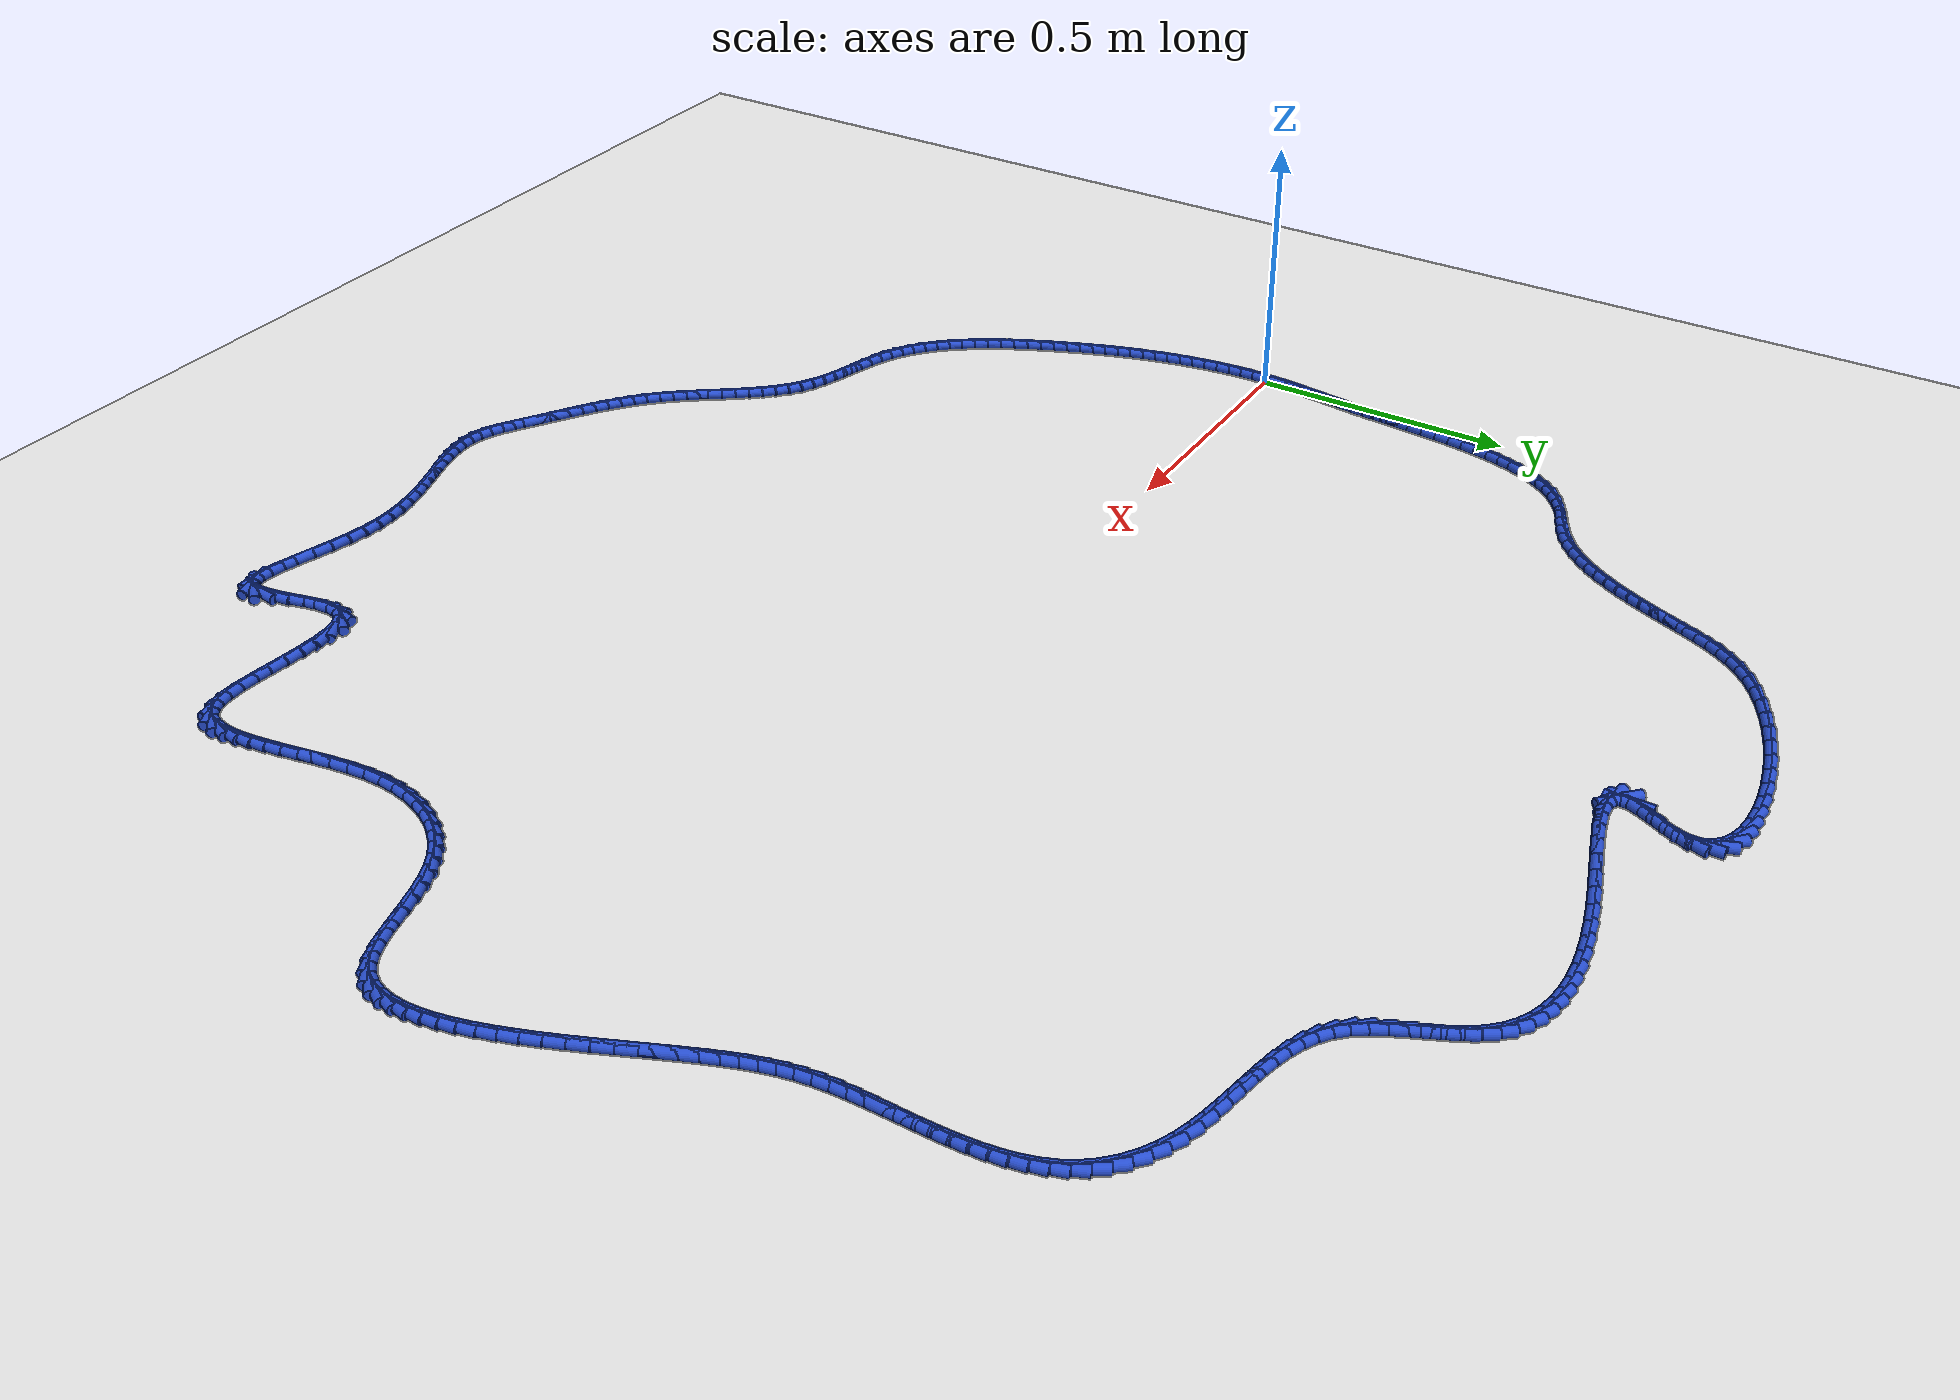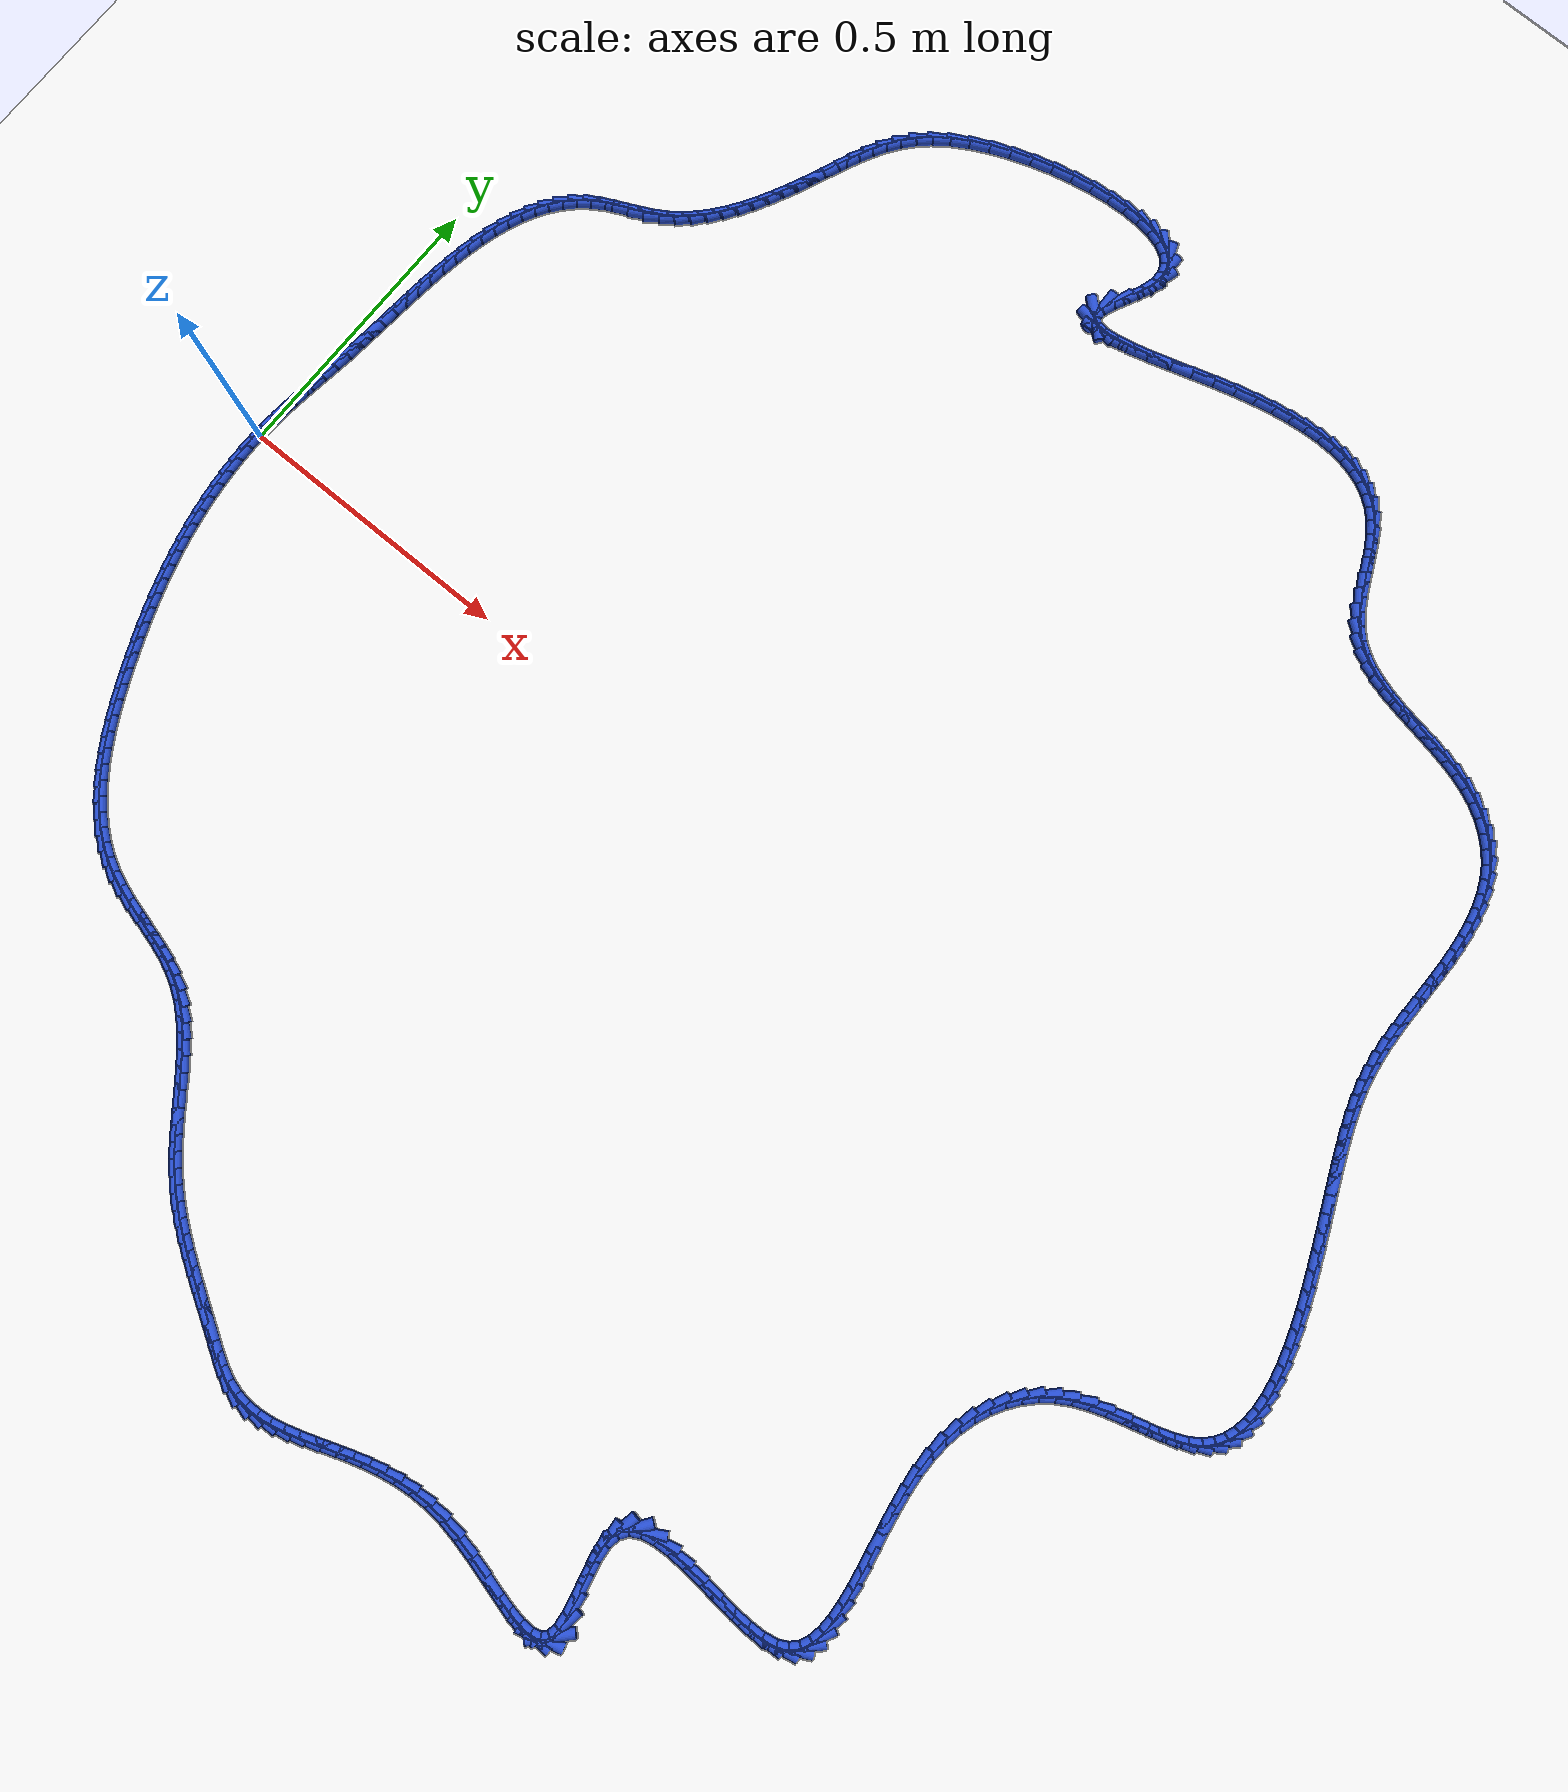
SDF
<sdf version="1.6">
 <world name="default">
  <light name="sun" type="directional">
   <pose>0 0 10 0 -0 0</pose>
   <diffuse>0.8 0.8 0.8 1</diffuse>
   <specular>0.2 0.2 0.2 1</specular>
   <attenuation>
    <range>1000</range>
    <constant>0.9</constant>
    <linear>0.01</linear>
    <quadratic>0.001</quadratic>
   </attenuation>
   <direction>-0.5 0.1 -0.9</direction>
  </light>
  <model name="ground_plane">
   <static>1</static>
   <link name="link">
    <collision name="collision">
     <geometry><plane><normal>0 0 1</normal><size>100 100</size></plane></geometry>
     <surface><friction><ode><mu>100</mu><mu2>50</mu2></ode></friction></surface>
    </collision>
    <visual name="visual">
     <cast_shadows>0</cast_shadows>
     <geometry><plane><normal>0 0 1</normal><size>100 100</size></plane></geometry>
     <material>
      <script><uri>file://media/materials/scripts/gazebo.material</uri><name>Gazebo/WhiteGlow</name></script>
     </material>
    </visual>
   </link>
  </model>
  <gravity>0 0 -9.8</gravity>
  <magnetic_field>6e-06 2.3e-05 -4.2e-05</magnetic_field>
  <atmosphere type="adiabatic"/>
  <physics name="default_physics" default="0" type="ode">
   <max_step_size>0.001</max_step_size>
   <real_time_factor>1</real_time_factor>
   <real_time_update_rate>1000</real_time_update_rate>
  </physics>
  <scene><ambient>0.4 0.4 0.4 1</ambient><background>0.7 0.7 0.7 1</background><shadows>1</shadows></scene>
  <spherical_coordinates>
   <surface_model>EARTH_WGS84</surface_model>
   <latitude_deg>0</latitude_deg>
   <longitude_deg>0</longitude_deg>
   <elevation>0</elevation>
   <heading_deg>0</heading_deg>
  </spherical_coordinates>
  <model name="line">
   <link name="link_0">
    <pose>1.734723475976807e-18 9.71445146547012e-17 0.01 0 1.57 1.5256166260533213</pose>
    <collision name="collision">
     <geometry><cylinder><radius>0.01</radius><length>0.08</length></cylinder></geometry>
    </collision>
    <visual name="visual">
     <material>
      <script><name>Gazebo/Blue</name><uri>file://media/materials/scripts/gazebo.material</uri></script>
     </material>
     <geometry><cylinder><radius>0.01</radius><length>0.08</length></cylinder></geometry>
    </visual>
   </link>
   <link name="link_1">
    <pose>0.00116869647694062 0.025850131062630347 0.01 0 1.57 1.493957417507516</pose>
    <collision name="collision">
     <geometry><cylinder><radius>0.01</radius><length>0.08</length></cylinder></geometry>
    </collision>
    <visual name="visual">
     <material>
      <script><name>Gazebo/Blue</name><uri>file://media/materials/scripts/gazebo.material</uri></script>
     </material>
     <geometry><cylinder><radius>0.01</radius><length>0.08</length></cylinder></geometry>
    </visual>
   </link>
   <link name="link_2">
    <pose>0.003148059794446102 0.05155932280931687 0.01 0 1.57 1.4689957960236688</pose>
    <collision name="collision">
     <geometry><cylinder><radius>0.01</radius><length>0.08</length></cylinder></geometry>
    </collision>
    <visual name="visual">
     <material>
      <script><name>Gazebo/Blue</name><uri>file://media/materials/scripts/gazebo.material</uri></script>
     </material>
     <geometry><cylinder><radius>0.01</radius><length>0.08</length></cylinder></geometry>
    </visual>
   </link>
   <link name="link_3">
    <pose>0.005771656131429956 0.0772421652142144 0.01 0 1.57 1.4510282856935357</pose>
    <collision name="collision">
     <geometry><cylinder><radius>0.01</radius><length>0.08</length></cylinder></geometry>
    </collision>
    <visual name="visual">
     <material>
      <script><name>Gazebo/Blue</name><uri>file://media/materials/scripts/gazebo.material</uri></script>
     </material>
     <geometry><cylinder><radius>0.01</radius><length>0.08</length></cylinder></geometry>
    </visual>
   </link>
   <link name="link_4">
    <pose>0.008873051666805689 0.10301324825147767 0.01 0 1.57 1.4401528353001605</pose>
    <collision name="collision">
     <geometry><cylinder><radius>0.01</radius><length>0.08</length></cylinder></geometry>
    </collision>
    <visual name="visual">
     <material>
      <script><name>Gazebo/Blue</name><uri>file://media/materials/scripts/gazebo.material</uri></script>
     </material>
     <geometry><cylinder><radius>0.01</radius><length>0.08</length></cylinder></geometry>
    </visual>
   </link>
   <link name="link_5">
    <pose>0.012285812579486808 0.1289871618952615 0.01 0 1.57 1.4362952401775806</pose>
    <collision name="collision">
     <geometry><cylinder><radius>0.01</radius><length>0.08</length></cylinder></geometry>
    </collision>
    <visual name="visual">
     <material>
      <script><name>Gazebo/Blue</name><uri>file://media/materials/scripts/gazebo.material</uri></script>
     </material>
     <geometry><cylinder><radius>0.01</radius><length>0.08</length></cylinder></geometry>
    </visual>
   </link>
   <link name="link_6">
    <pose>0.015843505048386823 0.1552784961197205 0.01 0 1.57 1.439234777435147</pose>
    <collision name="collision">
     <geometry><cylinder><radius>0.01</radius><length>0.08</length></cylinder></geometry>
    </collision>
    <visual name="visual">
     <material>
      <script><name>Gazebo/Blue</name><uri>file://media/materials/scripts/gazebo.material</uri></script>
     </material>
     <geometry><cylinder><radius>0.01</radius><length>0.08</length></cylinder></geometry>
    </visual>
   </link>
   <link name="link_7">
    <pose>0.019379695252419237 0.1820018408990096 0.01 0 1.57 1.4486259576093121</pose>
    <collision name="collision">
     <geometry><cylinder><radius>0.01</radius><length>0.08</length></cylinder></geometry>
    </collision>
    <visual name="visual">
     <material>
      <script><name>Gazebo/Blue</name><uri>file://media/materials/scripts/gazebo.material</uri></script>
     </material>
     <geometry><cylinder><radius>0.01</radius><length>0.08</length></cylinder></geometry>
    </visual>
   </link>
   <link name="link_8">
    <pose>0.022727949370497557 0.2092717862072834 0.01 0 1.57 1.462984772046113</pose>
    <collision name="collision">
     <geometry><cylinder><radius>0.01</radius><length>0.08</length></cylinder></geometry>
    </collision>
    <visual name="visual">
     <material>
      <script><name>Gazebo/Blue</name><uri>file://media/materials/scripts/gazebo.material</uri></script>
     </material>
     <geometry><cylinder><radius>0.01</radius><length>0.08</length></cylinder></geometry>
    </visual>
   </link>
   <link name="link_9">
    <pose>0.025748484541219707 0.23717995621318205 0.01 0 1.57 1.474349265018024</pose>
    <collision name="collision">
     <geometry><cylinder><radius>0.01</radius><length>0.08</length></cylinder></geometry>
    </collision>
    <visual name="visual">
     <material>
      <script><name>Gazebo/Blue</name><uri>file://media/materials/scripts/gazebo.material</uri></script>
     </material>
     <geometry><cylinder><radius>0.01</radius><length>0.08</length></cylinder></geometry>
    </visual>
   </link>
   <link name="link_10">
    <pose>0.02850238716425009 0.2656448809664795 0.01 0 1.57 1.479580359231853</pose>
    <collision name="collision">
     <geometry><cylinder><radius>0.01</radius><length>0.08</length></cylinder></geometry>
    </collision>
    <visual name="visual">
     <material>
      <script><name>Gazebo/Blue</name><uri>file://media/materials/scripts/gazebo.material</uri></script>
     </material>
     <geometry><cylinder><radius>0.01</radius><length>0.08</length></cylinder></geometry>
    </visual>
   </link>
   <link name="link_11">
    <pose>0.03114232370157301 0.2945061736627289 0.01 0 1.57 1.4789799135891375</pose>
    <collision name="collision">
     <geometry><cylinder><radius>0.01</radius><length>0.08</length></cylinder></geometry>
    </collision>
    <visual name="visual">
     <material>
      <script><name>Gazebo/Blue</name><uri>file://media/materials/scripts/gazebo.material</uri></script>
     </material>
     <geometry><cylinder><radius>0.01</radius><length>0.08</length></cylinder></geometry>
    </visual>
   </link>
   <link name="link_12">
    <pose>0.03382142686987387 0.32360304571402376 0.01 0 1.57 1.4726811566009064</pose>
    <collision name="collision">
     <geometry><cylinder><radius>0.01</radius><length>0.08</length></cylinder></geometry>
    </collision>
    <visual name="visual">
     <material>
      <script><name>Gazebo/Blue</name><uri>file://media/materials/scripts/gazebo.material</uri></script>
     </material>
     <geometry><cylinder><radius>0.01</radius><length>0.08</length></cylinder></geometry>
    </visual>
   </link>
   <link name="link_13">
    <pose>0.036692829385838066 0.3527747085324575 0.01 0 1.57 1.460645369507437</pose>
    <collision name="collision">
     <geometry><cylinder><radius>0.01</radius><length>0.08</length></cylinder></geometry>
    </collision>
    <visual name="visual">
     <material>
      <script><name>Gazebo/Blue</name><uri>file://media/materials/scripts/gazebo.material</uri></script>
     </material>
     <geometry><cylinder><radius>0.01</radius><length>0.08</length></cylinder></geometry>
    </visual>
   </link>
   <link name="link_14">
    <pose>0.03990966396615103 0.38186037353012386 0.01 0 1.57 1.4426690949858585</pose>
    <collision name="collision">
     <geometry><cylinder><radius>0.01</radius><length>0.08</length></cylinder></geometry>
    </collision>
    <visual name="visual">
     <material>
      <script><name>Gazebo/Blue</name><uri>file://media/materials/scripts/gazebo.material</uri></script>
     </material>
     <geometry><cylinder><radius>0.01</radius><length>0.08</length></cylinder></geometry>
    </visual>
   </link>
   <link name="link_15">
    <pose>0.04362506332749818 0.41069925211911623 0.01 0 1.57 1.4183857987984956</pose>
    <collision name="collision">
     <geometry><cylinder><radius>0.01</radius><length>0.08</length></cylinder></geometry>
    </collision>
    <visual name="visual">
     <material>
      <script><name>Gazebo/Blue</name><uri>file://media/materials/scripts/gazebo.material</uri></script>
     </material>
     <geometry><cylinder><radius>0.01</radius><length>0.08</length></cylinder></geometry>
    </visual>
   </link>
   <link name="link_16">
    <pose>0.047992160186564936 0.43913055571152826 0.01 0 1.57 1.3872648616722052</pose>
    <collision name="collision">
     <geometry><cylinder><radius>0.01</radius><length>0.08</length></cylinder></geometry>
    </collision>
    <visual name="visual">
     <material>
      <script><name>Gazebo/Blue</name><uri>file://media/materials/scripts/gazebo.material</uri></script>
     </material>
     <geometry><cylinder><radius>0.01</radius><length>0.08</length></cylinder></geometry>
    </visual>
   </link>
   <link name="link_17">
    <pose>0.053164087260036685 0.46699349571945337 0.01 0 1.57 1.348612536292012</pose>
    <collision name="collision">
     <geometry><cylinder><radius>0.01</radius><length>0.08</length></cylinder></geometry>
    </collision>
    <visual name="visual">
     <material>
      <script><name>Gazebo/Blue</name><uri>file://media/materials/scripts/gazebo.material</uri></script>
     </material>
     <geometry><cylinder><radius>0.01</radius><length>0.08</length></cylinder></geometry>
    </visual>
   </link>
   <link name="link_18">
    <pose>0.059293977264598854 0.4941272835549851 0.01 0 1.57 1.3015826711993168</pose>
    <collision name="collision">
     <geometry><cylinder><radius>0.01</radius><length>0.08</length></cylinder></geometry>
    </collision>
    <visual name="visual">
     <material>
      <script><name>Gazebo/Blue</name><uri>file://media/materials/scripts/gazebo.material</uri></script>
     </material>
     <geometry><cylinder><radius>0.01</radius><length>0.08</length></cylinder></geometry>
    </visual>
   </link>
   <link name="link_19">
    <pose>0.06653496291693686 0.520371130630217 0.01 0 1.57 1.2452100775448491</pose>
    <collision name="collision">
     <geometry><cylinder><radius>0.01</radius><length>0.08</length></cylinder></geometry>
    </collision>
    <visual name="visual">
     <material>
      <script><name>Gazebo/Blue</name><uri>file://media/materials/scripts/gazebo.material</uri></script>
     </material>
     <geometry><cylinder><radius>0.01</radius><length>0.08</length></cylinder></geometry>
    </visual>
   </link>
   <link name="link_20">
    <pose>0.07504017693373613 0.5455642483572426 0.01 0 1.57 1.1784862851304385</pose>
    <collision name="collision">
     <geometry><cylinder><radius>0.01</radius><length>0.08</length></cylinder></geometry>
    </collision>
    <visual name="visual">
     <material>
      <script><name>Gazebo/Blue</name><uri>file://media/materials/scripts/gazebo.material</uri></script>
     </material>
     <geometry><cylinder><radius>0.01</radius><length>0.08</length></cylinder></geometry>
    </visual>
   </link>
   <link name="link_21">
    <pose>0.08496275203168208 0.5695458481481555 0.01 0 1.57 1.100503893631696</pose>
    <collision name="collision">
     <geometry><cylinder><radius>0.01</radius><length>0.08</length></cylinder></geometry>
    </collision>
    <visual name="visual">
     <material>
      <script><name>Gazebo/Blue</name><uri>file://media/materials/scripts/gazebo.material</uri></script>
     </material>
     <geometry><cylinder><radius>0.01</radius><length>0.08</length></cylinder></geometry>
    </visual>
   </link>
   <link name="link_22">
    <pose>0.09645582092746005 0.5921551414150488 0.01 0 1.57 1.0106947418961427</pose>
    <collision name="collision">
     <geometry><cylinder><radius>0.01</radius><length>0.08</length></cylinder></geometry>
    </collision>
    <visual name="visual">
     <material>
      <script><name>Gazebo/Blue</name><uri>file://media/materials/scripts/gazebo.material</uri></script>
     </material>
     <geometry><cylinder><radius>0.01</radius><length>0.08</length></cylinder></geometry>
    </visual>
   </link>
   <link name="link_23">
    <pose>0.10967251633775552 0.6132313395700165 0.01 0 1.57 0.9091644628190584</pose>
    <collision name="collision">
     <geometry><cylinder><radius>0.01</radius><length>0.08</length></cylinder></geometry>
    </collision>
    <visual name="visual">
     <material>
      <script><name>Gazebo/Blue</name><uri>file://media/materials/scripts/gazebo.material</uri></script>
     </material>
     <geometry><cylinder><radius>0.01</radius><length>0.08</length></cylinder></geometry>
    </visual>
   </link>
   <link name="link_24">
    <pose>0.12476597097925393 0.632613654025152 0.01 0 1.57 0.7970652830925509</pose>
    <collision name="collision">
     <geometry><cylinder><radius>0.01</radius><length>0.08</length></cylinder></geometry>
    </collision>
    <visual name="visual">
     <material>
      <script><name>Gazebo/Blue</name><uri>file://media/materials/scripts/gazebo.material</uri></script>
     </material>
     <geometry><cylinder><radius>0.01</radius><length>0.08</length></cylinder></geometry>
    </visual>
   </link>
   <link name="link_25">
    <pose>0.1418893175686407 0.650141296192549 0.01 0 1.57 0.6768560873420214</pose>
    <collision name="collision">
     <geometry><cylinder><radius>0.01</radius><length>0.08</length></cylinder></geometry>
    </collision>
    <visual name="visual">
     <material>
      <script><name>Gazebo/Blue</name><uri>file://media/materials/scripts/gazebo.material</uri></script>
     </material>
     <geometry><cylinder><radius>0.01</radius><length>0.08</length></cylinder></geometry>
    </visual>
   </link>
   <link name="link_26">
    <pose>0.16119568882260113 0.6656534774843008 0.01 0 1.57 0.5550580872785529</pose>
    <collision name="collision">
     <geometry><cylinder><radius>0.01</radius><length>0.08</length></cylinder></geometry>
    </collision>
    <visual name="visual">
     <material>
      <script><name>Gazebo/Blue</name><uri>file://media/materials/scripts/gazebo.material</uri></script>
     </material>
     <geometry><cylinder><radius>0.01</radius><length>0.08</length></cylinder></geometry>
    </visual>
   </link>
   <link name="link_27">
    <pose>0.182788204559637 0.679042701418995 0.01 0 1.57 0.4692039540594988</pose>
    <collision name="collision">
     <geometry><cylinder><radius>0.01</radius><length>0.08</length></cylinder></geometry>
    </collision>
    <visual name="visual">
     <material>
      <script><name>Gazebo/Blue</name><uri>file://media/materials/scripts/gazebo.material</uri></script>
     </material>
     <geometry><cylinder><radius>0.01</radius><length>0.08</length></cylinder></geometry>
    </visual>
   </link>
   <link name="link_28">
    <pose>0.20613460839057637 0.690878507594972 0.01 0 1.57 0.4385508027406525</pose>
    <collision name="collision">
     <geometry><cylinder><radius>0.01</radius><length>0.08</length></cylinder></geometry>
    </collision>
    <visual name="visual">
     <material>
      <script><name>Gazebo/Blue</name><uri>file://media/materials/scripts/gazebo.material</uri></script>
     </material>
     <geometry><cylinder><radius>0.01</radius><length>0.08</length></cylinder></geometry>
    </visual>
   </link>
   <link name="link_29">
    <pose>0.2302655471547311 0.70219619161636 0.01 0 1.57 0.45947059804062507</pose>
    <collision name="collision">
     <geometry><cylinder><radius>0.01</radius><length>0.08</length></cylinder></geometry>
    </collision>
    <visual name="visual">
     <material>
      <script><name>Gazebo/Blue</name><uri>file://media/materials/scripts/gazebo.material</uri></script>
     </material>
     <geometry><cylinder><radius>0.01</radius><length>0.08</length></cylinder></geometry>
    </visual>
   </link>
   <link name="link_30">
    <pose>0.25420305835117973 0.7140402229183036 0.01 0 1.57 0.532251332192737</pose>
    <collision name="collision">
     <geometry><cylinder><radius>0.01</radius><length>0.08</length></cylinder></geometry>
    </collision>
    <visual name="visual">
     <material>
      <script><name>Gazebo/Blue</name><uri>file://media/materials/scripts/gazebo.material</uri></script>
     </material>
     <geometry><cylinder><radius>0.01</radius><length>0.08</length></cylinder></geometry>
    </visual>
   </link>
   <link name="link_31">
    <pose>0.2769731182681054 0.7274505409547506 0.01 0 1.57 0.6384898365629288</pose>
    <collision name="collision">
     <geometry><cylinder><radius>0.01</radius><length>0.08</length></cylinder></geometry>
    </collision>
    <visual name="visual">
     <material>
      <script><name>Gazebo/Blue</name><uri>file://media/materials/scripts/gazebo.material</uri></script>
     </material>
     <geometry><cylinder><radius>0.01</radius><length>0.08</length></cylinder></geometry>
    </visual>
   </link>
   <link name="link_32">
    <pose>0.2979748091717407 0.7430379779031943 0.01 0 1.57 0.7391589999462186</pose>
    <collision name="collision">
     <geometry><cylinder><radius>0.01</radius><length>0.08</length></cylinder></geometry>
    </collision>
    <visual name="visual">
     <material>
      <script><name>Gazebo/Blue</name><uri>file://media/materials/scripts/gazebo.material</uri></script>
     </material>
     <geometry><cylinder><radius>0.01</radius><length>0.08</length></cylinder></geometry>
    </visual>
   </link>
   <link name="link_33">
    <pose>0.3172819406254005 0.7606373655288242 0.01 0 1.57 0.8286654513053895</pose>
    <collision name="collision">
     <geometry><cylinder><radius>0.01</radius><length>0.08</length></cylinder></geometry>
    </collision>
    <visual name="visual">
     <material>
      <script><name>Gazebo/Blue</name><uri>file://media/materials/scripts/gazebo.material</uri></script>
     </material>
     <geometry><cylinder><radius>0.01</radius><length>0.08</length></cylinder></geometry>
    </visual>
   </link>
   <link name="link_34">
    <pose>0.3350393058747735 0.7800018976269011 0.01 0 1.57 0.9064747410652184</pose>
    <collision name="collision">
     <geometry><cylinder><radius>0.01</radius><length>0.08</length></cylinder></geometry>
    </collision>
    <visual name="visual">
     <material>
      <script><name>Gazebo/Blue</name><uri>file://media/materials/scripts/gazebo.material</uri></script>
     </material>
     <geometry><cylinder><radius>0.01</radius><length>0.08</length></cylinder></geometry>
    </visual>
   </link>
   <link name="link_35">
    <pose>0.3513916981655486 0.8008847679926853 0.01 0 1.57 0.9727800219091481</pose>
    <collision name="collision">
     <geometry><cylinder><radius>0.01</radius><length>0.08</length></cylinder></geometry>
    </collision>
    <visual name="visual">
     <material>
      <script><name>Gazebo/Blue</name><uri>file://media/materials/scripts/gazebo.material</uri></script>
     </material>
     <geometry><cylinder><radius>0.01</radius><length>0.08</length></cylinder></geometry>
    </visual>
   </link>
   <link name="link_36">
    <pose>0.3664839107434145 0.8230391704214376 0.01 0 1.57 1.0281798192425016</pose>
    <collision name="collision">
     <geometry><cylinder><radius>0.01</radius><length>0.08</length></cylinder></geometry>
    </collision>
    <visual name="visual">
     <material>
      <script><name>Gazebo/Blue</name><uri>file://media/materials/scripts/gazebo.material</uri></script>
     </material>
     <geometry><cylinder><radius>0.01</radius><length>0.08</length></cylinder></geometry>
    </visual>
   </link>
   <link name="link_37">
    <pose>0.3804607368540602 0.8462182987084192 0.01 0 1.57 1.073422070494423</pose>
    <collision name="collision">
     <geometry><cylinder><radius>0.01</radius><length>0.08</length></cylinder></geometry>
    </collision>
    <visual name="visual">
     <material>
      <script><name>Gazebo/Blue</name><uri>file://media/materials/scripts/gazebo.material</uri></script>
     </material>
     <geometry><cylinder><radius>0.01</radius><length>0.08</length></cylinder></geometry>
    </visual>
   </link>
   <link name="link_38">
    <pose>0.39346696974317397 0.8701753466488901 0.01 0 1.57 1.1092301784177665</pose>
    <collision name="collision">
     <geometry><cylinder><radius>0.01</radius><length>0.08</length></cylinder></geometry>
    </collision>
    <visual name="visual">
     <material>
      <script><name>Gazebo/Blue</name><uri>file://media/materials/scripts/gazebo.material</uri></script>
     </material>
     <geometry><cylinder><radius>0.01</radius><length>0.08</length></cylinder></geometry>
    </visual>
   </link>
   <link name="link_39">
    <pose>0.40564740265644483 0.894663508038111 0.01 0 1.57 1.1361950923245538</pose>
    <collision name="collision">
     <geometry><cylinder><radius>0.01</radius><length>0.08</length></cylinder></geometry>
    </collision>
    <visual name="visual">
     <material>
      <script><name>Gazebo/Blue</name><uri>file://media/materials/scripts/gazebo.material</uri></script>
     </material>
     <geometry><cylinder><radius>0.01</radius><length>0.08</length></cylinder></geometry>
    </visual>
   </link>
   <link name="link_40">
    <pose>0.41714682883956183 0.9194359766713431 0.01 0 1.57 1.1547092960968621</pose>
    <collision name="collision">
     <geometry><cylinder><radius>0.01</radius><length>0.08</length></cylinder></geometry>
    </collision>
    <visual name="visual">
     <material>
      <script><name>Gazebo/Blue</name><uri>file://media/materials/scripts/gazebo.material</uri></script>
     </material>
     <geometry><cylinder><radius>0.01</radius><length>0.08</length></cylinder></geometry>
    </visual>
   </link>
   <link name="link_41">
    <pose>0.4281100415382134 0.9442459463438466 0.01 0 1.57 1.164921048920446</pose>
    <collision name="collision">
     <geometry><cylinder><radius>0.01</radius><length>0.08</length></cylinder></geometry>
    </collision>
    <visual name="visual">
     <material>
      <script><name>Gazebo/Blue</name><uri>file://media/materials/scripts/gazebo.material</uri></script>
     </material>
     <geometry><cylinder><radius>0.01</radius><length>0.08</length></cylinder></geometry>
    </visual>
   </link>
   <link name="link_42">
    <pose>0.43868183399808847 0.9688466108508826 0.01 0 1.57 1.165722030070353</pose>
    <collision name="collision">
     <geometry><cylinder><radius>0.01</radius><length>0.08</length></cylinder></geometry>
    </collision>
    <visual name="visual">
     <material>
      <script><name>Gazebo/Blue</name><uri>file://media/materials/scripts/gazebo.material</uri></script>
     </material>
     <geometry><cylinder><radius>0.01</radius><length>0.08</length></cylinder></geometry>
    </visual>
   </link>
   <link name="link_43">
    <pose>0.44903976972058357 0.9930029499423543 0.01 0 1.57 1.1481923088561112</pose>
    <collision name="collision">
     <geometry><cylinder><radius>0.01</radius><length>0.08</length></cylinder></geometry>
    </collision>
    <visual name="visual">
     <material>
      <script><name>Gazebo/Blue</name><uri>file://media/materials/scripts/gazebo.material</uri></script>
     </material>
     <geometry><cylinder><radius>0.01</radius><length>0.08</length></cylinder></geometry>
    </visual>
   </link>
   <link name="link_44">
    <pose>0.4596428870624329 1.0165811769352082 0.01 0 1.57 1.1074367402879843</pose>
    <collision name="collision">
     <geometry><cylinder><radius>0.01</radius><length>0.08</length></cylinder></geometry>
    </collision>
    <visual name="visual">
     <material>
      <script><name>Gazebo/Blue</name><uri>file://media/materials/scripts/gazebo.material</uri></script>
     </material>
     <geometry><cylinder><radius>0.01</radius><length>0.08</length></cylinder></geometry>
    </visual>
   </link>
   <link name="link_45">
    <pose>0.4710935805921025 1.039499063786162 0.01 0 1.57 1.0438678880762704</pose>
    <collision name="collision">
     <geometry><cylinder><radius>0.01</radius><length>0.08</length></cylinder></geometry>
    </collision>
    <visual name="visual">
     <material>
      <script><name>Gazebo/Blue</name><uri>file://media/materials/scripts/gazebo.material</uri></script>
     </material>
     <geometry><cylinder><radius>0.01</radius><length>0.08</length></cylinder></geometry>
    </visual>
   </link>
   <link name="link_46">
    <pose>0.4839953834810206 1.0616747919550809 0.01 0 1.57 0.9597492011556852</pose>
    <collision name="collision">
     <geometry><cylinder><radius>0.01</radius><length>0.08</length></cylinder></geometry>
    </collision>
    <visual name="visual">
     <material>
      <script><name>Gazebo/Blue</name><uri>file://media/materials/scripts/gazebo.material</uri></script>
     </material>
     <geometry><cylinder><radius>0.01</radius><length>0.08</length></cylinder></geometry>
    </visual>
   </link>
   <link name="link_47">
    <pose>0.498951828900616 1.0830265429018318 0.01 0 1.57 0.859651599224505</pose>
    <collision name="collision">
     <geometry><cylinder><radius>0.01</radius><length>0.08</length></cylinder></geometry>
    </collision>
    <visual name="visual">
     <material>
      <script><name>Gazebo/Blue</name><uri>file://media/materials/scripts/gazebo.material</uri></script>
     </material>
     <geometry><cylinder><radius>0.01</radius><length>0.08</length></cylinder></geometry>
    </visual>
   </link>
   <link name="link_48">
    <pose>0.5165664500223166 1.103472498086279 0.01 0 1.57 0.7502570467437116</pose>
    <collision name="collision">
     <geometry><cylinder><radius>0.01</radius><length>0.08</length></cylinder></geometry>
    </collision>
    <visual name="visual">
     <material>
      <script><name>Gazebo/Blue</name><uri>file://media/materials/scripts/gazebo.material</uri></script>
     </material>
     <geometry><cylinder><radius>0.01</radius><length>0.08</length></cylinder></geometry>
    </visual>
   </link>
   <link name="link_49">
    <pose>0.5374427800175513 1.1229308389682897 0.01 0 1.57 0.6394661377737907</pose>
    <collision name="collision">
     <geometry><cylinder><radius>0.01</radius><length>0.08</length></cylinder></geometry>
    </collision>
    <visual name="visual">
     <material>
      <script><name>Gazebo/Blue</name><uri>file://media/materials/scripts/gazebo.material</uri></script>
     </material>
     <geometry><cylinder><radius>0.01</radius><length>0.08</length></cylinder></geometry>
    </visual>
   </link>
   <link name="link_50">
    <pose>0.562167015864104 1.1413186078487751 0.01 0 1.57 0.5416287361199237</pose>
    <collision name="collision">
     <geometry><cylinder><radius>0.01</radius><length>0.08</length></cylinder></geometry>
    </collision>
    <visual name="visual">
     <material>
      <script><name>Gazebo/Blue</name><uri>file://media/materials/scripts/gazebo.material</uri></script>
     </material>
     <geometry><cylinder><radius>0.01</radius><length>0.08</length></cylinder></geometry>
    </visual>
   </link>
   <link name="link_51">
    <pose>0.5907492566686642 1.1585149917149844 0.01 0 1.57 0.46267410280138355</pose>
    <collision name="collision">
     <geometry><cylinder><radius>0.01</radius><length>0.08</length></cylinder></geometry>
    </collision>
    <visual name="visual">
     <material>
      <script><name>Gazebo/Blue</name><uri>file://media/materials/scripts/gazebo.material</uri></script>
     </material>
     <geometry><cylinder><radius>0.01</radius><length>0.08</length></cylinder></geometry>
    </visual>
   </link>
   <link name="link_52">
    <pose>0.6225033749372363 1.1743534285978305 0.01 0 1.57 0.3963330868034903</pose>
    <collision name="collision">
     <geometry><cylinder><radius>0.01</radius><length>0.08</length></cylinder></geometry>
    </collision>
    <visual name="visual">
     <material>
      <script><name>Gazebo/Blue</name><uri>file://media/materials/scripts/gazebo.material</uri></script>
     </material>
     <geometry><cylinder><radius>0.01</radius><length>0.08</length></cylinder></geometry>
    </visual>
   </link>
   <link name="link_53">
    <pose>0.6567016107463863 1.1886646208668863 0.01 0 1.57 0.3377792730375458</pose>
    <collision name="collision">
     <geometry><cylinder><radius>0.01</radius><length>0.08</length></cylinder></geometry>
    </collision>
    <visual name="visual">
     <material>
      <script><name>Gazebo/Blue</name><uri>file://media/materials/scripts/gazebo.material</uri></script>
     </material>
     <geometry><cylinder><radius>0.01</radius><length>0.08</length></cylinder></geometry>
    </visual>
   </link>
   <link name="link_54">
    <pose>0.692616204172679 1.201279270891723 0.01 0 1.57 0.28342894368360994</pose>
    <collision name="collision">
     <geometry><cylinder><radius>0.01</radius><length>0.08</length></cylinder></geometry>
    </collision>
    <visual name="visual">
     <material>
      <script><name>Gazebo/Blue</name><uri>file://media/materials/scripts/gazebo.material</uri></script>
     </material>
     <geometry><cylinder><radius>0.01</radius><length>0.08</length></cylinder></geometry>
    </visual>
   </link>
   <link name="link_55">
    <pose>0.7295193952926812 1.2120280810419126 0.01 0 1.57 0.23030511879337834</pose>
    <collision name="collision">
     <geometry><cylinder><radius>0.01</radius><length>0.08</length></cylinder></geometry>
    </collision>
    <visual name="visual">
     <material>
      <script><name>Gazebo/Blue</name><uri>file://media/materials/scripts/gazebo.material</uri></script>
     </material>
     <geometry><cylinder><radius>0.01</radius><length>0.08</length></cylinder></geometry>
    </visual>
   </link>
   <link name="link_56">
    <pose>0.766683424182958 1.2207417536870269 0.01 0 1.57 0.1755514905643811</pose>
    <collision name="collision">
     <geometry><cylinder><radius>0.01</radius><length>0.08</length></cylinder></geometry>
    </collision>
    <visual name="visual">
     <material>
      <script><name>Gazebo/Blue</name><uri>file://media/materials/scripts/gazebo.material</uri></script>
     </material>
     <geometry><cylinder><radius>0.01</radius><length>0.08</length></cylinder></geometry>
    </visual>
   </link>
   <link name="link_57">
    <pose>0.8033805309200753 1.2272509911966383 0.01 0 1.57 0.11596252953802715</pose>
    <collision name="collision">
     <geometry><cylinder><radius>0.01</radius><length>0.08</length></cylinder></geometry>
    </collision>
    <visual name="visual">
     <material>
      <script><name>Gazebo/Blue</name><uri>file://media/materials/scripts/gazebo.material</uri></script>
     </material>
     <geometry><cylinder><radius>0.01</radius><length>0.08</length></cylinder></geometry>
    </visual>
   </link>
   <link name="link_58">
    <pose>0.8388829555805991 1.231386495940318 0.01 0 1.57 0.047387819163450744</pose>
    <collision name="collision">
     <geometry><cylinder><radius>0.01</radius><length>0.08</length></cylinder></geometry>
    </collision>
    <visual name="visual">
     <material>
      <script><name>Gazebo/Blue</name><uri>file://media/materials/scripts/gazebo.material</uri></script>
     </material>
     <geometry><cylinder><radius>0.01</radius><length>0.08</length></cylinder></geometry>
    </visual>
   </link>
   <link name="link_59">
    <pose>0.8724629382410944 1.2329789702876384 0.01 0 1.57 -0.036190516044978985</pose>
    <collision name="collision">
     <geometry><cylinder><radius>0.01</radius><length>0.08</length></cylinder></geometry>
    </collision>
    <visual name="visual">
     <material>
      <script><name>Gazebo/Blue</name><uri>file://media/materials/scripts/gazebo.material</uri></script>
     </material>
     <geometry><cylinder><radius>0.01</radius><length>0.08</length></cylinder></geometry>
    </visual>
   </link>
   <link name="link_60">
    <pose>0.9033927189781276 1.231859116608171 0.01 0 1.57 -0.14422625214484894</pose>
    <collision name="collision">
     <geometry><cylinder><radius>0.01</radius><length>0.08</length></cylinder></geometry>
    </collision>
    <visual name="visual">
     <material>
      <script><name>Gazebo/Blue</name><uri>file://media/materials/scripts/gazebo.material</uri></script>
     </material>
     <geometry><cylinder><radius>0.01</radius><length>0.08</length></cylinder></geometry>
    </visual>
   </link>
   <link name="link_61">
    <pose>0.9309445378682641 1.227857637271488 0.01 0 1.57 -0.2921834049710707</pose>
    <collision name="collision">
     <geometry><cylinder><radius>0.01</radius><length>0.08</length></cylinder></geometry>
    </collision>
    <visual name="visual">
     <material>
      <script><name>Gazebo/Blue</name><uri>file://media/materials/scripts/gazebo.material</uri></script>
     </material>
     <geometry><cylinder><radius>0.01</radius><length>0.08</length></cylinder></geometry>
    </visual>
   </link>
   <link name="link_62">
    <pose>0.9543906349880698 1.220805234647161 0.01 0 1.57 -0.5043139969758289</pose>
    <collision name="collision">
     <geometry><cylinder><radius>0.01</radius><length>0.08</length></cylinder></geometry>
    </collision>
    <visual name="visual">
     <material>
      <script><name>Gazebo/Blue</name><uri>file://media/materials/scripts/gazebo.material</uri></script>
     </material>
     <geometry><cylinder><radius>0.01</radius><length>0.08</length></cylinder></geometry>
    </visual>
   </link>
   <link name="link_63">
    <pose>0.9730032504141105 1.210532611104762 0.01 0 1.57 -0.8082578233585817</pose>
    <collision name="collision">
     <geometry><cylinder><radius>0.01</radius><length>0.08</length></cylinder></geometry>
    </collision>
    <visual name="visual">
     <material>
      <script><name>Gazebo/Blue</name><uri>file://media/materials/scripts/gazebo.material</uri></script>
     </material>
     <geometry><cylinder><radius>0.01</radius><length>0.08</length></cylinder></geometry>
    </visual>
   </link>
   <link name="link_64">
    <pose>0.9860546242229519 1.1968704690138634 0.01 0 1.57 -1.1966138454430713</pose>
    <collision name="collision">
     <geometry><cylinder><radius>0.01</radius><length>0.08</length></cylinder></geometry>
    </collision>
    <visual name="visual">
     <material>
      <script><name>Gazebo/Blue</name><uri>file://media/materials/scripts/gazebo.material</uri></script>
     </material>
     <geometry><cylinder><radius>0.01</radius><length>0.08</length></cylinder></geometry>
    </visual>
   </link>
   <link name="link_65">
    <pose>0.9928169964911593 1.1796495107440361 0.01 0 1.57 1.5586537033834686</pose>
    <collision name="collision">
     <geometry><cylinder><radius>0.01</radius><length>0.08</length></cylinder></geometry>
    </collision>
    <visual name="visual">
     <material>
      <script><name>Gazebo/Blue</name><uri>file://media/materials/scripts/gazebo.material</uri></script>
     </material>
     <geometry><cylinder><radius>0.01</radius><length>0.08</length></cylinder></geometry>
    </visual>
   </link>
   <link name="link_66">
    <pose>0.9925626072952989 1.1587004386648527 0.01 0 1.57 1.2690001442227676</pose>
    <collision name="collision">
     <geometry><cylinder><radius>0.01</radius><length>0.08</length></cylinder></geometry>
    </collision>
    <visual name="visual">
     <material>
      <script><name>Gazebo/Blue</name><uri>file://media/materials/scripts/gazebo.material</uri></script>
     </material>
     <geometry><cylinder><radius>0.01</radius><length>0.08</length></cylinder></geometry>
    </visual>
   </link>
   <link name="link_67">
    <pose>0.9848858580511837 1.1340405735744503 0.01 0 1.57 1.1351473967602748</pose>
    <collision name="collision">
     <geometry><cylinder><radius>0.01</radius><length>0.08</length></cylinder></geometry>
    </collision>
    <visual name="visual">
     <material>
      <script><name>Gazebo/Blue</name><uri>file://media/materials/scripts/gazebo.material</uri></script>
     </material>
     <geometry><cylinder><radius>0.01</radius><length>0.08</length></cylinder></geometry>
    </visual>
   </link>
   <link name="link_68">
    <pose>0.9725397291450519 1.1075169066011745 0.01 0 1.57 1.1159459665035485</pose>
    <collision name="collision">
     <geometry><cylinder><radius>0.01</radius><length>0.08</length></cylinder></geometry>
    </collision>
    <visual name="visual">
     <material>
      <script><name>Gazebo/Blue</name><uri>file://media/materials/scripts/gazebo.material</uri></script>
     </material>
     <geometry><cylinder><radius>0.01</radius><length>0.08</length></cylinder></geometry>
    </visual>
   </link>
   <link name="link_69">
    <pose>0.9600671545562722 1.08201329545561 0.01 0 1.57 1.2144565226582074</pose>
    <collision name="collision">
     <geometry><cylinder><radius>0.01</radius><length>0.08</length></cylinder></geometry>
    </collision>
    <visual name="visual">
     <material>
      <script><name>Gazebo/Blue</name><uri>file://media/materials/scripts/gazebo.material</uri></script>
     </material>
     <geometry><cylinder><radius>0.01</radius><length>0.08</length></cylinder></geometry>
    </visual>
   </link>
   <link name="link_70">
    <pose>0.9520315110617423 1.0604254397495434 0.01 0 1.57 -1.5397284438039578</pose>
    <collision name="collision">
     <geometry><cylinder><radius>0.01</radius><length>0.08</length></cylinder></geometry>
    </collision>
    <visual name="visual">
     <material>
      <script><name>Gazebo/Blue</name><uri>file://media/materials/scripts/gazebo.material</uri></script>
     </material>
     <geometry><cylinder><radius>0.01</radius><length>0.08</length></cylinder></geometry>
    </visual>
   </link>
   <link name="link_71">
    <pose>0.9525009719395982 1.0453194917527076 0.01 0 1.57 -0.7347622642415702</pose>
    <collision name="collision">
     <geometry><cylinder><radius>0.01</radius><length>0.08</length></cylinder></geometry>
    </collision>
    <visual name="visual">
     <material>
      <script><name>Gazebo/Blue</name><uri>file://media/materials/scripts/gazebo.material</uri></script>
     </material>
     <geometry><cylinder><radius>0.01</radius><length>0.08</length></cylinder></geometry>
    </visual>
   </link>
   <link name="link_72">
    <pose>0.9618938753666514 1.0368327165004294 0.01 0 1.57 -0.16320870271021212</pose>
    <collision name="collision">
     <geometry><cylinder><radius>0.01</radius><length>0.08</length></cylinder></geometry>
    </collision>
    <visual name="visual">
     <material>
      <script><name>Gazebo/Blue</name><uri>file://media/materials/scripts/gazebo.material</uri></script>
     </material>
     <geometry><cylinder><radius>0.01</radius><length>0.08</length></cylinder></geometry>
    </visual>
   </link>
   <link name="link_73">
    <pose>0.9789966084901018 1.034016350505387 0.01 0 1.57 0.08037353765980317</pose>
    <collision name="collision">
     <geometry><cylinder><radius>0.01</radius><length>0.08</length></cylinder></geometry>
    </collision>
    <visual name="visual">
     <material>
      <script><name>Gazebo/Blue</name><uri>file://media/materials/scripts/gazebo.material</uri></script>
     </material>
     <geometry><cylinder><radius>0.01</radius><length>0.08</length></cylinder></geometry>
    </visual>
   </link>
   <link name="link_74">
    <pose>1.002587944121631 1.0359165631027492 0.01 0 1.57 0.19376846875348608</pose>
    <collision name="collision">
     <geometry><cylinder><radius>0.01</radius><length>0.08</length></cylinder></geometry>
    </collision>
    <visual name="visual">
     <material>
      <script><name>Gazebo/Blue</name><uri>file://media/materials/scripts/gazebo.material</uri></script>
     </material>
     <geometry><cylinder><radius>0.01</radius><length>0.08</length></cylinder></geometry>
    </visual>
   </link>
   <link name="link_75">
    <pose>1.0314466550729204 1.0415795236276857 0.01 0 1.57 0.25199291635664633</pose>
    <collision name="collision">
     <geometry><cylinder><radius>0.01</radius><length>0.08</length></cylinder></geometry>
    </collision>
    <visual name="visual">
     <material>
      <script><name>Gazebo/Blue</name><uri>file://media/materials/scripts/gazebo.material</uri></script>
     </material>
     <geometry><cylinder><radius>0.01</radius><length>0.08</length></cylinder></geometry>
    </visual>
   </link>
   <link name="link_76">
    <pose>1.0643515141556517 1.0500514014153648 0.01 0 1.57 0.2813620786361187</pose>
    <collision name="collision">
     <geometry><cylinder><radius>0.01</radius><length>0.08</length></cylinder></geometry>
    </collision>
    <visual name="visual">
     <material>
      <script><name>Gazebo/Blue</name><uri>file://media/materials/scripts/gazebo.material</uri></script>
     </material>
     <geometry><cylinder><radius>0.01</radius><length>0.08</length></cylinder></geometry>
    </visual>
   </link>
   <link name="link_77">
    <pose>1.1000812941815075 1.0603783658009567 0.01 0 1.57 0.2921491000549135</pose>
    <collision name="collision">
     <geometry><cylinder><radius>0.01</radius><length>0.08</length></cylinder></geometry>
    </collision>
    <visual name="visual">
     <material>
      <script><name>Gazebo/Blue</name><uri>file://media/materials/scripts/gazebo.material</uri></script>
     </material>
     <geometry><cylinder><radius>0.01</radius><length>0.08</length></cylinder></geometry>
    </visual>
   </link>
   <link name="link_78">
    <pose>1.1374147679621693 1.07160658611963 0.01 0 1.57 0.2880689051992741</pose>
    <collision name="collision">
     <geometry><cylinder><radius>0.01</radius><length>0.08</length></cylinder></geometry>
    </collision>
    <visual name="visual">
     <material>
      <script><name>Gazebo/Blue</name><uri>file://media/materials/scripts/gazebo.material</uri></script>
     </material>
     <geometry><cylinder><radius>0.01</radius><length>0.08</length></cylinder></geometry>
    </visual>
   </link>
   <link name="link_79">
    <pose>1.1751307083093185 1.0827822317065539 0.01 0 1.57 0.26925253856919273</pose>
    <collision name="collision">
     <geometry><cylinder><radius>0.01</radius><length>0.08</length></cylinder></geometry>
    </collision>
    <visual name="visual">
     <material>
      <script><name>Gazebo/Blue</name><uri>file://media/materials/scripts/gazebo.material</uri></script>
     </material>
     <geometry><cylinder><radius>0.01</radius><length>0.08</length></cylinder></geometry>
    </visual>
   </link>
   <link name="link_80">
    <pose>1.2120247513012237 1.0929632752781082 0.01 0 1.57 0.23867908906135366</pose>
    <collision name="collision">
     <geometry><cylinder><radius>0.01</radius><length>0.08</length></cylinder></geometry>
    </collision>
    <visual name="visual">
     <material>
      <script><name>Gazebo/Blue</name><uri>file://media/materials/scripts/gazebo.material</uri></script>
     </material>
     <geometry><cylinder><radius>0.01</radius><length>0.08</length></cylinder></geometry>
    </visual>
   </link>
   <link name="link_81">
    <pose>1.2474170606443942 1.10157483072823 0.01 0 1.57 0.2011450879656559</pose>
    <collision name="collision">
     <geometry><cylinder><radius>0.01</radius><length>0.08</length></cylinder></geometry>
    </collision>
    <visual name="visual">
     <material>
      <script><name>Gazebo/Blue</name><uri>file://media/materials/scripts/gazebo.material</uri></script>
     </material>
     <geometry><cylinder><radius>0.01</radius><length>0.08</length></cylinder></geometry>
    </visual>
   </link>
   <link name="link_82">
    <pose>1.2812417982576054 1.108471777733496 0.01 0 1.57 0.15579319072140588</pose>
    <collision name="collision">
     <geometry><cylinder><radius>0.01</radius><length>0.08</length></cylinder></geometry>
    </collision>
    <visual name="visual">
     <material>
      <script><name>Gazebo/Blue</name><uri>file://media/materials/scripts/gazebo.material</uri></script>
     </material>
     <geometry><cylinder><radius>0.01</radius><length>0.08</length></cylinder></geometry>
    </visual>
   </link>
   <link name="link_83">
    <pose>1.3134680226957354 1.113533421742134 0.01 0 1.57 0.10115598374585874</pose>
    <collision name="collision">
     <geometry><cylinder><radius>0.01</radius><length>0.08</length></cylinder></geometry>
    </collision>
    <visual name="visual">
     <material>
      <script><name>Gazebo/Blue</name><uri>file://media/materials/scripts/gazebo.material</uri></script>
     </material>
     <geometry><cylinder><radius>0.01</radius><length>0.08</length></cylinder></geometry>
    </visual>
   </link>
   <link name="link_84">
    <pose>1.3440647925136622 1.1166390682023715 0.01 0 1.57 0.03554422569072332</pose>
    <collision name="collision">
     <geometry><cylinder><radius>0.01</radius><length>0.08</length></cylinder></geometry>
    </collision>
    <visual name="visual">
     <material>
      <script><name>Gazebo/Blue</name><uri>file://media/materials/scripts/gazebo.material</uri></script>
     </material>
     <geometry><cylinder><radius>0.01</radius><length>0.08</length></cylinder></geometry>
    </visual>
   </link>
   <link name="link_85">
    <pose>1.373001166266262 1.1176680225624354 0.01 0 1.57 -0.04285979796544012</pose>
    <collision name="collision">
     <geometry><cylinder><radius>0.01</radius><length>0.08</length></cylinder></geometry>
    </collision>
    <visual name="visual">
     <material>
      <script><name>Gazebo/Blue</name><uri>file://media/materials/scripts/gazebo.material</uri></script>
     </material>
     <geometry><cylinder><radius>0.01</radius><length>0.08</length></cylinder></geometry>
    </visual>
   </link>
   <link name="link_86">
    <pose>1.400246202508415 1.116499590270553 0.01 0 1.57 -0.1357637881752329</pose>
    <collision name="collision">
     <geometry><cylinder><radius>0.01</radius><length>0.08</length></cylinder></geometry>
    </collision>
    <visual name="visual">
     <material>
      <script><name>Gazebo/Blue</name><uri>file://media/materials/scripts/gazebo.material</uri></script>
     </material>
     <geometry><cylinder><radius>0.01</radius><length>0.08</length></cylinder></geometry>
    </visual>
   </link>
   <link name="link_87">
    <pose>1.4257689597949978 1.1130130767749522 0.01 0 1.57 -0.24430165773730167</pose>
    <collision name="collision">
     <geometry><cylinder><radius>0.01</radius><length>0.08</length></cylinder></geometry>
    </collision>
    <visual name="visual">
     <material>
      <script><name>Gazebo/Blue</name><uri>file://media/materials/scripts/gazebo.material</uri></script>
     </material>
     <geometry><cylinder><radius>0.01</radius><length>0.08</length></cylinder></geometry>
    </visual>
   </link>
   <link name="link_88">
    <pose>1.4495384966808886 1.1070877875238598 0.01 0 1.57 -0.36831630921177866</pose>
    <collision name="collision">
     <geometry><cylinder><radius>0.01</radius><length>0.08</length></cylinder></geometry>
    </collision>
    <visual name="visual">
     <material>
      <script><name>Gazebo/Blue</name><uri>file://media/materials/scripts/gazebo.material</uri></script>
     </material>
     <geometry><cylinder><radius>0.01</radius><length>0.08</length></cylinder></geometry>
    </visual>
   </link>
   <link name="link_89">
    <pose>1.471523871720965 1.0986030279655032 0.01 0 1.57 -0.5055521476734737</pose>
    <collision name="collision">
     <geometry><cylinder><radius>0.01</radius><length>0.08</length></cylinder></geometry>
    </collision>
    <visual name="visual">
     <material>
      <script><name>Gazebo/Blue</name><uri>file://media/materials/scripts/gazebo.material</uri></script>
     </material>
     <geometry><cylinder><radius>0.01</radius><length>0.08</length></cylinder></geometry>
    </visual>
   </link>
   <link name="link_90">
    <pose>1.4916941434701054 1.0874381035481102 0.01 0 1.57 -0.651230977815713</pose>
    <collision name="collision">
     <geometry><cylinder><radius>0.01</radius><length>0.08</length></cylinder></geometry>
    </collision>
    <visual name="visual">
     <material>
      <script><name>Gazebo/Blue</name><uri>file://media/materials/scripts/gazebo.material</uri></script>
     </material>
     <geometry><cylinder><radius>0.01</radius><length>0.08</length></cylinder></geometry>
    </visual>
   </link>
   <link name="link_91">
    <pose>1.5100183704831867 1.0734723197199074 0.01 0 1.57 -0.7985998119423762</pose>
    <collision name="collision">
     <geometry><cylinder><radius>0.01</radius><length>0.08</length></cylinder></geometry>
    </collision>
    <visual name="visual">
     <material>
      <script><name>Gazebo/Blue</name><uri>file://media/materials/scripts/gazebo.material</uri></script>
     </material>
     <geometry><cylinder><radius>0.01</radius><length>0.08</length></cylinder></geometry>
    </visual>
   </link>
   <link name="link_92">
    <pose>1.5264656113150874 1.0565849819291233 0.01 0 1.57 -0.939232094600086</pose>
    <collision name="collision">
     <geometry><cylinder><radius>0.01</radius><length>0.08</length></cylinder></geometry>
    </collision>
    <visual name="visual">
     <material>
      <script><name>Gazebo/Blue</name><uri>file://media/materials/scripts/gazebo.material</uri></script>
     </material>
     <geometry><cylinder><radius>0.01</radius><length>0.08</length></cylinder></geometry>
    </visual>
   </link>
   <link name="link_93">
    <pose>1.541023194390251 1.0366843404555288 0.01 0 1.57 -1.0460801497887524</pose>
    <collision name="collision">
     <geometry><cylinder><radius>0.01</radius><length>0.08</length></cylinder></geometry>
    </collision>
    <visual name="visual">
     <material>
      <script><name>Gazebo/Blue</name><uri>file://media/materials/scripts/gazebo.material</uri></script>
     </material>
     <geometry><cylinder><radius>0.01</radius><length>0.08</length></cylinder></geometry>
    </visual>
   </link>
   <link name="link_94">
    <pose>1.5540234503953603 1.0142252303438934 0.01 0 1.57 -1.1056395041748535</pose>
    <collision name="collision">
     <geometry><cylinder><radius>0.01</radius><length>0.08</length></cylinder></geometry>
    </collision>
    <visual name="visual">
     <material>
      <script><name>Gazebo/Blue</name><uri>file://media/materials/scripts/gazebo.material</uri></script>
     </material>
     <geometry><cylinder><radius>0.01</radius><length>0.08</length></cylinder></geometry>
    </visual>
   </link>
   <link name="link_95">
    <pose>1.5661064776580764 0.990150080843808 0.01 0 1.57 -1.1250691606056618</pose>
    <collision name="collision">
     <geometry><cylinder><radius>0.01</radius><length>0.08</length></cylinder></geometry>
    </collision>
    <visual name="visual">
     <material>
      <script><name>Gazebo/Blue</name><uri>file://media/materials/scripts/gazebo.material</uri></script>
     </material>
     <geometry><cylinder><radius>0.01</radius><length>0.08</length></cylinder></geometry>
    </visual>
   </link>
   <link name="link_96">
    <pose>1.577923166989865 0.9654184196644063 0.01 0 1.57 -1.1075771709890136</pose>
    <collision name="collision">
     <geometry><cylinder><radius>0.01</radius><length>0.08</length></cylinder></geometry>
    </collision>
    <visual name="visual">
     <material>
      <script><name>Gazebo/Blue</name><uri>file://media/materials/scripts/gazebo.material</uri></script>
     </material>
     <geometry><cylinder><radius>0.01</radius><length>0.08</length></cylinder></geometry>
    </visual>
   </link>
   <link name="link_97">
    <pose>1.5901244092021902 0.9409897745148232 0.01 0 1.57 -1.0516855634457887</pose>
    <collision name="collision">
     <geometry><cylinder><radius>0.01</radius><length>0.08</length></cylinder></geometry>
    </collision>
    <visual name="visual">
     <material>
      <script><name>Gazebo/Blue</name><uri>file://media/materials/scripts/gazebo.material</uri></script>
     </material>
     <geometry><cylinder><radius>0.01</radius><length>0.08</length></cylinder></geometry>
    </visual>
   </link>
   <link name="link_98">
    <pose>1.6033610951065178 0.9178236731041933 0.01 0 1.57 -0.9517176344220338</pose>
    <collision name="collision">
     <geometry><cylinder><radius>0.01</radius><length>0.08</length></cylinder></geometry>
    </collision>
    <visual name="visual">
     <material>
      <script><name>Gazebo/Blue</name><uri>file://media/materials/scripts/gazebo.material</uri></script>
     </material>
     <geometry><cylinder><radius>0.01</radius><length>0.08</length></cylinder></geometry>
    </visual>
   </link>
   <link name="link_99">
    <pose>1.6182841155143128 0.8968796431416508 0.01 0 1.57 -0.8017544807335152</pose>
    <collision name="collision">
     <geometry><cylinder><radius>0.01</radius><length>0.08</length></cylinder></geometry>
    </collision>
    <visual name="visual">
     <material>
      <script><name>Gazebo/Blue</name><uri>file://media/materials/scripts/gazebo.material</uri></script>
     </material>
     <geometry><cylinder><radius>0.01</radius><length>0.08</length></cylinder></geometry>
    </visual>
   </link>
   <link name="link_100">
    <pose>1.6355159116438671 0.8790747242732585 0.01 0 1.57 -0.6356002564603009</pose>
    <collision name="collision">
     <geometry><cylinder><radius>0.01</radius><length>0.08</length></cylinder></geometry>
    </collision>
    <visual name="visual">
     <material>
      <script><name>Gazebo/Blue</name><uri>file://media/materials/scripts/gazebo.material</uri></script>
     </material>
     <geometry><cylinder><radius>0.01</radius><length>0.08</length></cylinder></geometry>
    </visual>
   </link>
   <link name="link_101">
    <pose>1.6551742411855659 0.8645722362083997 0.01 0 1.57 -0.4925867406405621</pose>
    <collision name="collision">
     <geometry><cylinder><radius>0.01</radius><length>0.08</length></cylinder></geometry>
    </collision>
    <visual name="visual">
     <material>
      <script><name>Gazebo/Blue</name><uri>file://media/materials/scripts/gazebo.material</uri></script>
     </material>
     <geometry><cylinder><radius>0.01</radius><length>0.08</length></cylinder></geometry>
    </visual>
   </link>
   <link name="link_102">
    <pose>1.6769435222394942 0.8528883273689005 0.01 0 1.57 -0.37867386024666994</pose>
    <collision name="collision">
     <geometry><cylinder><radius>0.01</radius><length>0.08</length></cylinder></geometry>
    </collision>
    <visual name="visual">
     <material>
      <script><name>Gazebo/Blue</name><uri>file://media/materials/scripts/gazebo.material</uri></script>
     </material>
     <geometry><cylinder><radius>0.01</radius><length>0.08</length></cylinder></geometry>
    </visual>
   </link>
   <link name="link_103">
    <pose>1.7004940960816686 0.843518123134708 0.01 0 1.57 -0.2936830649587683</pose>
    <collision name="collision">
     <geometry><cylinder><radius>0.01</radius><length>0.08</length></cylinder></geometry>
    </collision>
    <visual name="visual">
     <material>
      <script><name>Gazebo/Blue</name><uri>file://media/materials/scripts/gazebo.material</uri></script>
     </material>
     <geometry><cylinder><radius>0.01</radius><length>0.08</length></cylinder></geometry>
    </visual>
   </link>
   <link name="link_104">
    <pose>1.7254963039881084 0.8359567488857692 0.01 0 1.57 -0.23509666714366115</pose>
    <collision name="collision">
     <geometry><cylinder><radius>0.01</radius><length>0.08</length></cylinder></geometry>
    </collision>
    <visual name="visual">
     <material>
      <script><name>Gazebo/Blue</name><uri>file://media/materials/scripts/gazebo.material</uri></script>
     </material>
     <geometry><cylinder><radius>0.01</radius><length>0.08</length></cylinder></geometry>
    </visual>
   </link>
   <link name="link_105">
    <pose>1.7516204872348309 0.8296993300020309 0.01 0 1.57 -0.20007470644073472</pose>
    <collision name="collision">
     <geometry><cylinder><radius>0.01</radius><length>0.08</length></cylinder></geometry>
    </collision>
    <visual name="visual">
     <material>
      <script><name>Gazebo/Blue</name><uri>file://media/materials/scripts/gazebo.material</uri></script>
     </material>
     <geometry><cylinder><radius>0.01</radius><length>0.08</length></cylinder></geometry>
    </visual>
   </link>
   <link name="link_106">
    <pose>1.778536987097855 0.8242409918634401 0.01 0 1.57 -0.18642529350978923</pose>
    <collision name="collision">
     <geometry><cylinder><radius>0.01</radius><length>0.08</length></cylinder></geometry>
    </collision>
    <visual name="visual">
     <material>
      <script><name>Gazebo/Blue</name><uri>file://media/materials/scripts/gazebo.material</uri></script>
     </material>
     <geometry><cylinder><radius>0.01</radius><length>0.08</length></cylinder></geometry>
    </visual>
   </link>
   <link name="link_107">
    <pose>1.8059161448531984 0.819076859849944 0.01 0 1.57 -0.19293096035353363</pose>
    <collision name="collision">
     <geometry><cylinder><radius>0.01</radius><length>0.08</length></cylinder></geometry>
    </collision>
    <visual name="visual">
     <material>
      <script><name>Gazebo/Blue</name><uri>file://media/materials/scripts/gazebo.material</uri></script>
     </material>
     <geometry><cylinder><radius>0.01</radius><length>0.08</length></cylinder></geometry>
    </visual>
   </link>
   <link name="link_108">
    <pose>1.8334283017768798 0.8137020593414895 0.01 0 1.57 -0.21937469631753076</pose>
    <collision name="collision">
     <geometry><cylinder><radius>0.01</radius><length>0.08</length></cylinder></geometry>
    </collision>
    <visual name="visual">
     <material>
      <script><name>Gazebo/Blue</name><uri>file://media/materials/scripts/gazebo.material</uri></script>
     </material>
     <geometry><cylinder><radius>0.01</radius><length>0.08</length></cylinder></geometry>
    </visual>
   </link>
   <link name="link_109">
    <pose>1.860743799144917 0.8076117157180235 0.01 0 1.57 -0.26641261627031837</pose>
    <collision name="collision">
     <geometry><cylinder><radius>0.01</radius><length>0.08</length></cylinder></geometry>
    </collision>
    <visual name="visual">
     <material>
      <script><name>Gazebo/Blue</name><uri>file://media/materials/scripts/gazebo.material</uri></script>
     </material>
     <geometry><cylinder><radius>0.01</radius><length>0.08</length></cylinder></geometry>
    </visual>
   </link>
   <link name="link_110">
    <pose>1.8875329782333288 0.8003009543594929 0.01 0 1.57 -0.33528056452423133</pose>
    <collision name="collision">
     <geometry><cylinder><radius>0.01</radius><length>0.08</length></cylinder></geometry>
    </collision>
    <visual name="visual">
     <material>
      <script><name>Gazebo/Blue</name><uri>file://media/materials/scripts/gazebo.material</uri></script>
     </material>
     <geometry><cylinder><radius>0.01</radius><length>0.08</length></cylinder></geometry>
    </visual>
   </link>
   <link name="link_111">
    <pose>1.913466180318133 0.7912649006458448 0.01 0 1.57 -0.42720664627439814</pose>
    <collision name="collision">
     <geometry><cylinder><radius>0.01</radius><length>0.08</length></cylinder></geometry>
    </collision>
    <visual name="visual">
     <material>
      <script><name>Gazebo/Blue</name><uri>file://media/materials/scripts/gazebo.material</uri></script>
     </material>
     <geometry><cylinder><radius>0.01</radius><length>0.08</length></cylinder></geometry>
    </visual>
   </link>
   <link name="link_112">
    <pose>1.9382137407977864 0.7799987110487203 0.01 0 1.57 -0.5378786523895778</pose>
    <collision name="collision">
     <geometry><cylinder><radius>0.01</radius><length>0.08</length></cylinder></geometry>
    </collision>
    <visual name="visual">
     <material>
      <script><name>Gazebo/Blue</name><uri>file://media/materials/scripts/gazebo.material</uri></script>
     </material>
     <geometry><cylinder><radius>0.01</radius><length>0.08</length></cylinder></geometry>
    </visual>
   </link>
   <link name="link_113">
    <pose>1.9614157448701406 0.766157562492252 0.01 0 1.57 -0.6534319787543768</pose>
    <collision name="collision">
     <geometry><cylinder><radius>0.01</radius><length>0.08</length></cylinder></geometry>
    </collision>
    <visual name="visual">
     <material>
      <script><name>Gazebo/Blue</name><uri>file://media/materials/scripts/gazebo.material</uri></script>
     </material>
     <geometry><cylinder><radius>0.01</radius><length>0.08</length></cylinder></geometry>
    </visual>
   </link>
   <link name="link_114">
    <pose>1.9826115801939752 0.7499293115338902 0.01 0 1.57 -0.7748291459596391</pose>
    <collision name="collision">
     <geometry><cylinder><radius>0.01</radius><length>0.08</length></cylinder></geometry>
    </collision>
    <visual name="visual">
     <material>
      <script><name>Gazebo/Blue</name><uri>file://media/materials/scripts/gazebo.material</uri></script>
     </material>
     <geometry><cylinder><radius>0.01</radius><length>0.08</length></cylinder></geometry>
    </visual>
   </link>
   <link name="link_115">
    <pose>2.0013197075404197 0.7316125158161726 0.01 0 1.57 -0.9059943664940129</pose>
    <collision name="collision">
     <geometry><cylinder><radius>0.01</radius><length>0.08</length></cylinder></geometry>
    </collision>
    <visual name="visual">
     <material>
      <script><name>Gazebo/Blue</name><uri>file://media/materials/scripts/gazebo.material</uri></script>
     </material>
     <geometry><cylinder><radius>0.01</radius><length>0.08</length></cylinder></geometry>
    </visual>
   </link>
   <link name="link_116">
    <pose>2.017083032495335 0.7115018250949771 0.01 0 1.57 -1.0381903825209495</pose>
    <collision name="collision">
     <geometry><cylinder><radius>0.01</radius><length>0.08</length></cylinder></geometry>
    </collision>
    <visual name="visual">
     <material>
      <script><name>Gazebo/Blue</name><uri>file://media/materials/scripts/gazebo.material</uri></script>
     </material>
     <geometry><cylinder><radius>0.01</radius><length>0.08</length></cylinder></geometry>
    </visual>
   </link>
   <link name="link_117">
    <pose>2.0298595363424385 0.6898255327720768 0.01 0 1.57 -1.1583223849385311</pose>
    <collision name="collision">
     <geometry><cylinder><radius>0.01</radius><length>0.08</length></cylinder></geometry>
    </collision>
    <visual name="visual">
     <material>
      <script><name>Gazebo/Blue</name><uri>file://media/materials/scripts/gazebo.material</uri></script>
     </material>
     <geometry><cylinder><radius>0.01</radius><length>0.08</length></cylinder></geometry>
    </visual>
   </link>
   <link name="link_118">
    <pose>2.039953986551203 0.6667564930436735 0.01 0 1.57 -1.2627819025740536</pose>
    <collision name="collision">
     <geometry><cylinder><radius>0.01</radius><length>0.08</length></cylinder></geometry>
    </collision>
    <visual name="visual">
     <material>
      <script><name>Gazebo/Blue</name><uri>file://media/materials/scripts/gazebo.material</uri></script>
     </material>
     <geometry><cylinder><radius>0.01</radius><length>0.08</length></cylinder></geometry>
    </visual>
   </link>
   <link name="link_119">
    <pose>2.047681799016848 0.6424658577882632 0.01 0 1.57 -1.3504268026802349</pose>
    <collision name="collision">
     <geometry><cylinder><radius>0.01</radius><length>0.08</length></cylinder></geometry>
    </collision>
    <visual name="visual">
     <material>
      <script><name>Gazebo/Blue</name><uri>file://media/materials/scripts/gazebo.material</uri></script>
     </material>
     <geometry><cylinder><radius>0.01</radius><length>0.08</length></cylinder></geometry>
    </visual>
   </link>
   <link name="link_120">
    <pose>2.053358389634596 0.6171247788843434 0.01 0 1.57 -1.4216181048584207</pose>
    <collision name="collision">
     <geometry><cylinder><radius>0.01</radius><length>0.08</length></cylinder></geometry>
    </collision>
    <visual name="visual">
     <material>
      <script><name>Gazebo/Blue</name><uri>file://media/materials/scripts/gazebo.material</uri></script>
     </material>
     <geometry><cylinder><radius>0.01</radius><length>0.08</length></cylinder></geometry>
    </visual>
   </link>
   <link name="link_121">
    <pose>2.0572991742996662 0.5909044082104101 0.01 0 1.57 -1.477472436813044</pose>
    <collision name="collision">
     <geometry><cylinder><radius>0.01</radius><length>0.08</length></cylinder></geometry>
    </collision>
    <visual name="visual">
     <material>
      <script><name>Gazebo/Blue</name><uri>file://media/materials/scripts/gazebo.material</uri></script>
     </material>
     <geometry><cylinder><radius>0.01</radius><length>0.08</length></cylinder></geometry>
    </visual>
   </link>
   <link name="link_122">
    <pose>2.05981956890728 0.5639758976449606 0.01 0 1.57 -1.519307386661663</pose>
    <collision name="collision">
     <geometry><cylinder><radius>0.01</radius><length>0.08</length></cylinder></geometry>
    </collision>
    <visual name="visual">
     <material>
      <script><name>Gazebo/Blue</name><uri>file://media/materials/scripts/gazebo.material</uri></script>
     </material>
     <geometry><cylinder><radius>0.01</radius><length>0.08</length></cylinder></geometry>
    </visual>
   </link>
   <link name="link_123">
    <pose>2.0612349893526583 0.5365103990664912 0.01 0 1.57 -1.5483124352320383</pose>
    <collision name="collision">
     <geometry><cylinder><radius>0.01</radius><length>0.08</length></cylinder></geometry>
    </collision>
    <visual name="visual">
     <material>
      <script><name>Gazebo/Blue</name><uri>file://media/materials/scripts/gazebo.material</uri></script>
     </material>
     <geometry><cylinder><radius>0.01</radius><length>0.08</length></cylinder></geometry>
    </visual>
   </link>
   <link name="link_124">
    <pose>2.061860851531021 0.5086790643534987 0.01 0 1.57 -1.5653828456777732</pose>
    <collision name="collision">
     <geometry><cylinder><radius>0.01</radius><length>0.08</length></cylinder></geometry>
    </collision>
    <visual name="visual">
     <material>
      <script><name>Gazebo/Blue</name><uri>file://media/materials/scripts/gazebo.material</uri></script>
     </material>
     <geometry><cylinder><radius>0.01</radius><length>0.08</length></cylinder></geometry>
    </visual>
   </link>
   <link name="link_125">
    <pose>2.06201257133759 0.4806530453844791 0.01 0 1.57 1.5705465306476307</pose>
    <collision name="collision">
     <geometry><cylinder><radius>0.01</radius><length>0.08</length></cylinder></geometry>
    </collision>
    <visual name="visual">
     <material>
      <script><name>Gazebo/Blue</name><uri>file://media/materials/scripts/gazebo.material</uri></script>
     </material>
     <geometry><cylinder><radius>0.01</radius><length>0.08</length></cylinder></geometry>
    </visual>
   </link>
   <link name="link_126">
    <pose>2.0620055646675852 0.4526034940379294 0.01 0 1.57 -1.56543177664147</pose>
    <collision name="collision">
     <geometry><cylinder><radius>0.01</radius><length>0.08</length></cylinder></geometry>
    </collision>
    <visual name="visual">
     <material>
      <script><name>Gazebo/Blue</name><uri>file://media/materials/scripts/gazebo.material</uri></script>
     </material>
     <geometry><cylinder><radius>0.01</radius><length>0.08</length></cylinder></geometry>
    </visual>
   </link>
   <link name="link_127">
    <pose>2.0621552474162277 0.4247015621923463 0.01 0 1.57 -1.5482578372812867</pose>
    <collision name="collision">
     <geometry><cylinder><radius>0.01</radius><length>0.08</length></cylinder></geometry>
    </collision>
    <visual name="visual">
     <material>
      <script><name>Gazebo/Blue</name><uri>file://media/materials/scripts/gazebo.material</uri></script>
     </material>
     <geometry><cylinder><radius>0.01</radius><length>0.08</length></cylinder></geometry>
    </visual>
   </link>
   <link name="link_128">
    <pose>2.0627770354787387 0.39711840172622626 0.01 0 1.57 -1.518826153145357</pose>
    <collision name="collision">
     <geometry><cylinder><radius>0.01</radius><length>0.08</length></cylinder></geometry>
    </collision>
    <visual name="visual">
     <material>
      <script><name>Gazebo/Blue</name><uri>file://media/materials/scripts/gazebo.material</uri></script>
     </material>
     <geometry><cylinder><radius>0.01</radius><length>0.08</length></cylinder></geometry>
    </visual>
   </link>
   <link name="link_129">
    <pose>2.0641863447503375 0.3700251645180659 0.01 0 1.57 -1.4760359260544635</pose>
    <collision name="collision">
     <geometry><cylinder><radius>0.01</radius><length>0.08</length></cylinder></geometry>
    </collision>
    <visual name="visual">
     <material>
      <script><name>Gazebo/Blue</name><uri>file://media/materials/scripts/gazebo.material</uri></script>
     </material>
     <geometry><cylinder><radius>0.01</radius><length>0.08</length></cylinder></geometry>
    </visual>
   </link>
   <link name="link_130">
    <pose>2.0666985911262463 0.343593002446362 0.01 0 1.57 -1.4192462014015974</pose>
    <collision name="collision">
     <geometry><cylinder><radius>0.01</radius><length>0.08</length></cylinder></geometry>
    </collision>
    <visual name="visual">
     <material>
      <script><name>Gazebo/Blue</name><uri>file://media/materials/scripts/gazebo.material</uri></script>
     </material>
     <geometry><cylinder><radius>0.01</radius><length>0.08</length></cylinder></geometry>
    </visual>
   </link>
   <link name="link_131">
    <pose>2.0706115934707103 0.31797112223829643 0.01 0 1.57 -1.358227458449177</pose>
    <collision name="collision">
     <geometry><cylinder><radius>0.01</radius><length>0.08</length></cylinder></geometry>
    </collision>
    <visual name="visual">
     <material>
      <script><name>Gazebo/Blue</name><uri>file://media/materials/scripts/gazebo.material</uri></script>
     </material>
     <geometry><cylinder><radius>0.01</radius><length>0.08</length></cylinder></geometry>
    </visual>
   </link>
   <link name="link_132">
    <pose>2.0759956928041854 0.2930250443725131 0.01 0 1.57 -1.3023745750225335</pose>
    <collision name="collision">
     <geometry><cylinder><radius>0.01</radius><length>0.08</length></cylinder></geometry>
    </collision>
    <visual name="visual">
     <material>
      <script><name>Gazebo/Blue</name><uri>file://media/materials/scripts/gazebo.material</uri></script>
     </material>
     <geometry><cylinder><radius>0.01</radius><length>0.08</length></cylinder></geometry>
    </visual>
   </link>
   <link name="link_133">
    <pose>2.0827628029694267 0.2684227157487979 0.01 0 1.57 -1.254155458404103</pose>
    <collision name="collision">
     <geometry><cylinder><radius>0.01</radius><length>0.08</length></cylinder></geometry>
    </collision>
    <visual name="visual">
     <material>
      <script><name>Gazebo/Blue</name><uri>file://media/materials/scripts/gazebo.material</uri></script>
     </material>
     <geometry><cylinder><radius>0.01</radius><length>0.08</length></cylinder></geometry>
    </visual>
   </link>
   <link name="link_134">
    <pose>2.0908216199740886 0.24382807032416778 0.01 0 1.57 -1.2150865741512633</pose>
    <collision name="collision">
     <geometry><cylinder><radius>0.01</radius><length>0.08</length></cylinder></geometry>
    </collision>
    <visual name="visual">
     <material>
      <script><name>Gazebo/Blue</name><uri>file://media/materials/scripts/gazebo.material</uri></script>
     </material>
     <geometry><cylinder><radius>0.01</radius><length>0.08</length></cylinder></geometry>
    </visual>
   </link>
   <link name="link_135">
    <pose>2.100080839825827 0.2189050420556414 0.01 0 1.57 -1.1858060812863538</pose>
    <collision name="collision">
     <geometry><cylinder><radius>0.01</radius><length>0.08</length></cylinder></geometry>
    </collision>
    <visual name="visual">
     <material>
      <script><name>Gazebo/Blue</name><uri>file://media/materials/scripts/gazebo.material</uri></script>
     </material>
     <geometry><cylinder><radius>0.01</radius><length>0.08</length></cylinder></geometry>
    </visual>
   </link>
   <link name="link_136">
    <pose>2.110449158532295 0.1933175649002367 0.01 0 1.57 -1.1661689161161561</pose>
    <collision name="collision">
     <geometry><cylinder><radius>0.01</radius><length>0.08</length></cylinder></geometry>
    </collision>
    <visual name="visual">
     <material>
      <script><name>Gazebo/Blue</name><uri>file://media/materials/scripts/gazebo.material</uri></script>
     </material>
     <geometry><cylinder><radius>0.01</radius><length>0.08</length></cylinder></geometry>
    </visual>
   </link>
   <link name="link_137">
    <pose>2.1218339251494007 0.16673370064642093 0.01 0 1.57 -1.1547405110036004</pose>
    <collision name="collision">
     <geometry><cylinder><radius>0.01</radius><length>0.08</length></cylinder></geometry>
    </collision>
    <visual name="visual">
     <material>
      <script><name>Gazebo/Blue</name><uri>file://media/materials/scripts/gazebo.material</uri></script>
     </material>
     <geometry><cylinder><radius>0.01</radius><length>0.08</length></cylinder></geometry>
    </visual>
   </link>
   <link name="link_138">
    <pose>2.134073466323942 0.13903303526813196 0.01 0 1.57 -1.1494315284132404</pose>
    <collision name="collision">
     <geometry><cylinder><radius>0.01</radius><length>0.08</length></cylinder></geometry>
    </collision>
    <visual name="visual">
     <material>
      <script><name>Gazebo/Blue</name><uri>file://media/materials/scripts/gazebo.material</uri></script>
     </material>
     <geometry><cylinder><radius>0.01</radius><length>0.08</length></cylinder></geometry>
    </visual>
   </link>
   <link name="link_139">
    <pose>2.1469054052794756 0.11040376769340454 0.01 0 1.57 -1.1493991488767341</pose>
    <collision name="collision">
     <geometry><cylinder><radius>0.01</radius><length>0.08</length></cylinder></geometry>
    </collision>
    <visual name="visual">
     <material>
      <script><name>Gazebo/Blue</name><uri>file://media/materials/scripts/gazebo.material</uri></script>
     </material>
     <geometry><cylinder><radius>0.01</radius><length>0.08</length></cylinder></geometry>
    </visual>
   </link>
   <link name="link_140">
    <pose>2.160059397285015 0.08105851522564902 0.01 0 1.57 -1.1542617133432242</pose>
    <collision name="collision">
     <geometry><cylinder><radius>0.01</radius><length>0.08</length></cylinder></geometry>
    </collision>
    <visual name="visual">
     <material>
      <script><name>Gazebo/Blue</name><uri>file://media/materials/scripts/gazebo.material</uri></script>
     </material>
     <geometry><cylinder><radius>0.01</radius><length>0.08</length></cylinder></geometry>
    </visual>
   </link>
   <link name="link_141">
    <pose>2.1732650976095735 0.05120989516827446 0.01 0 1.57 -1.1639387005230097</pose>
    <collision name="collision">
     <geometry><cylinder><radius>0.01</radius><length>0.08</length></cylinder></geometry>
    </collision>
    <visual name="visual">
     <material>
      <script><name>Gazebo/Blue</name><uri>file://media/materials/scripts/gazebo.material</uri></script>
     </material>
     <geometry><cylinder><radius>0.01</radius><length>0.08</length></cylinder></geometry>
    </visual>
   </link>
   <link name="link_142">
    <pose>2.186252161522162 0.021070524824691086 0.01 0 1.57 -1.17861757991251</pose>
    <collision name="collision">
     <geometry><cylinder><radius>0.01</radius><length>0.08</length></cylinder></geometry>
    </collision>
    <visual name="visual">
     <material>
      <script><name>Gazebo/Blue</name><uri>file://media/materials/scripts/gazebo.material</uri></script>
     </material>
     <geometry><cylinder><radius>0.01</radius><length>0.08</length></cylinder></geometry>
    </visual>
   </link>
   <link name="link_143">
    <pose>2.1987502442917943 -0.009146978501691137 0.01 0 1.57 -1.1987562000145573</pose>
    <collision name="collision">
     <geometry><cylinder><radius>0.01</radius><length>0.08</length></cylinder></geometry>
    </collision>
    <visual name="visual">
     <material>
      <script><name>Gazebo/Blue</name><uri>file://media/materials/scripts/gazebo.material</uri></script>
     </material>
     <geometry><cylinder><radius>0.01</radius><length>0.08</length></cylinder></geometry>
    </visual>
   </link>
   <link name="link_144">
    <pose>2.210489001187484 -0.039229997507462366 0.01 0 1.57 -1.22511702229926</pose>
    <collision name="collision">
     <geometry><cylinder><radius>0.01</radius><length>0.08</length></cylinder></geometry>
    </collision>
    <visual name="visual">
     <material>
      <script><name>Gazebo/Blue</name><uri>file://media/materials/scripts/gazebo.material</uri></script>
     </material>
     <geometry><cylinder><radius>0.01</radius><length>0.08</length></cylinder></geometry>
    </visual>
   </link>
   <link name="link_145">
    <pose>2.221198087478243 -0.06896591488921268 0.01 0 1.57 -1.258835107251744</pose>
    <collision name="collision">
     <geometry><cylinder><radius>0.01</radius><length>0.08</length></cylinder></geometry>
    </collision>
    <visual name="visual">
     <material>
      <script><name>Gazebo/Blue</name><uri>file://media/materials/scripts/gazebo.material</uri></script>
     </material>
     <geometry><cylinder><radius>0.01</radius><length>0.08</length></cylinder></geometry>
    </visual>
   </link>
   <link name="link_146">
    <pose>2.2306071584330835 -0.09814211334353215 0.01 0 1.57 -1.3015253641112232</pose>
    <collision name="collision">
     <geometry><cylinder><radius>0.01</radius><length>0.08</length></cylinder></geometry>
    </collision>
    <visual name="visual">
     <material>
      <script><name>Gazebo/Blue</name><uri>file://media/materials/scripts/gazebo.material</uri></script>
     </material>
     <geometry><cylinder><radius>0.01</radius><length>0.08</length></cylinder></geometry>
    </visual>
   </link>
   <link name="link_147">
    <pose>2.2384458693210196 -0.1265459755670109 0.01 0 1.57 -1.3554344568841672</pose>
    <collision name="collision">
     <geometry><cylinder><radius>0.01</radius><length>0.08</length></cylinder></geometry>
    </collision>
    <visual name="visual">
     <material>
      <script><name>Gazebo/Blue</name><uri>file://media/materials/scripts/gazebo.material</uri></script>
     </material>
     <geometry><cylinder><radius>0.01</radius><length>0.08</length></cylinder></geometry>
    </visual>
   </link>
   <link name="link_148">
    <pose>2.244443875411063 -0.15396488425623905 0.01 0 1.57 -1.4236316221638114</pose>
    <collision name="collision">
     <geometry><cylinder><radius>0.01</radius><length>0.08</length></cylinder></geometry>
    </collision>
    <visual name="visual">
     <material>
      <script><name>Gazebo/Blue</name><uri>file://media/materials/scripts/gazebo.material</uri></script>
     </material>
     <geometry><cylinder><radius>0.01</radius><length>0.08</length></cylinder></geometry>
    </visual>
   </link>
   <link name="link_149">
    <pose>2.248330831972227 -0.18018622210780671 0.01 0 1.57 -1.5101897656618217</pose>
    <collision name="collision">
     <geometry><cylinder><radius>0.01</radius><length>0.08</length></cylinder></geometry>
    </collision>
    <visual name="visual">
     <material>
      <script><name>Gazebo/Blue</name><uri>file://media/materials/scripts/gazebo.material</uri></script>
     </material>
     <geometry><cylinder><radius>0.01</radius><length>0.08</length></cylinder></geometry>
    </visual>
   </link>
   <link name="link_150">
    <pose>2.249836394273524 -0.20499737181830405 0.01 0 1.57 1.5214075223963521</pose>
    <collision name="collision">
     <geometry><cylinder><radius>0.01</radius><length>0.08</length></cylinder></geometry>
    </collision>
    <visual name="visual">
     <material>
      <script><name>Gazebo/Blue</name><uri>file://media/materials/scripts/gazebo.material</uri></script>
     </material>
     <geometry><cylinder><radius>0.01</radius><length>0.08</length></cylinder></geometry>
    </visual>
   </link>
   <link name="link_151">
    <pose>2.248690217583968 -0.22818571608432106 0.01 0 1.57 1.3825279454444908</pose>
    <collision name="collision">
     <geometry><cylinder><radius>0.01</radius><length>0.08</length></cylinder></geometry>
    </collision>
    <visual name="visual">
     <material>
      <script><name>Gazebo/Blue</name><uri>file://media/materials/scripts/gazebo.material</uri></script>
     </material>
     <geometry><cylinder><radius>0.01</radius><length>0.08</length></cylinder></geometry>
    </visual>
   </link>
   <link name="link_152">
    <pose>2.24462195717257 -0.24953863760244716 0.01 0 1.57 1.2110560425450028</pose>
    <collision name="collision">
     <geometry><cylinder><radius>0.01</radius><length>0.08</length></cylinder></geometry>
    </collision>
    <visual name="visual">
     <material>
      <script><name>Gazebo/Blue</name><uri>file://media/materials/scripts/gazebo.material</uri></script>
     </material>
     <geometry><cylinder><radius>0.01</radius><length>0.08</length></cylinder></geometry>
    </visual>
   </link>
   <link name="link_153">
    <pose>2.237361268308344 -0.268843519069274 0.01 0 1.57 1.0092145886800634</pose>
    <collision name="collision">
     <geometry><cylinder><radius>0.01</radius><length>0.08</length></cylinder></geometry>
    </collision>
    <visual name="visual">
     <material>
      <script><name>Gazebo/Blue</name><uri>file://media/materials/scripts/gazebo.material</uri></script>
     </material>
     <geometry><cylinder><radius>0.01</radius><length>0.08</length></cylinder></geometry>
    </visual>
   </link>
   <link name="link_154">
    <pose>2.2266378062603023 -0.2858877431813909 0.01 0 1.57 0.789338178329338</pose>
    <collision name="collision">
     <geometry><cylinder><radius>0.01</radius><length>0.08</length></cylinder></geometry>
    </collision>
    <visual name="visual">
     <material>
      <script><name>Gazebo/Blue</name><uri>file://media/materials/scripts/gazebo.material</uri></script>
     </material>
     <geometry><cylinder><radius>0.01</radius><length>0.08</length></cylinder></geometry>
    </visual>
   </link>
   <link name="link_155">
    <pose>2.2121812262974574 -0.3004586926353878 0.01 0 1.57 0.5784057601118012</pose>
    <collision name="collision">
     <geometry><cylinder><radius>0.01</radius><length>0.08</length></cylinder></geometry>
    </collision>
    <visual name="visual">
     <material>
      <script><name>Gazebo/Blue</name><uri>file://media/materials/scripts/gazebo.material</uri></script>
     </material>
     <geometry><cylinder><radius>0.01</radius><length>0.08</length></cylinder></geometry>
    </visual>
   </link>
   <link name="link_156">
    <pose>2.1938335038396235 -0.31243777868644734 0.01 0 1.57 0.4258750322062477</pose>
    <collision name="collision">
     <geometry><cylinder><radius>0.01</radius><length>0.08</length></cylinder></geometry>
    </collision>
    <visual name="visual">
     <material>
      <script><name>Gazebo/Blue</name><uri>file://media/materials/scripts/gazebo.material</uri></script>
     </material>
     <geometry><cylinder><radius>0.01</radius><length>0.08</length></cylinder></geometry>
    </visual>
   </link>
   <link name="link_157">
    <pose>2.172127234531675 -0.3222845637392524 0.01 0 1.57 0.33296841233727054</pose>
    <collision name="collision">
     <geometry><cylinder><radius>0.01</radius><length>0.08</length></cylinder></geometry>
    </collision>
    <visual name="visual">
     <material>
      <script><name>Gazebo/Blue</name><uri>file://media/materials/scripts/gazebo.material</uri></script>
     </material>
     <geometry><cylinder><radius>0.01</radius><length>0.08</length></cylinder></geometry>
    </visual>
   </link>
   <link name="link_158">
    <pose>2.1478573128639797 -0.33067819307997437 0.01 0 1.57 0.2846990485611873</pose>
    <collision name="collision">
     <geometry><cylinder><radius>0.01</radius><length>0.08</length></cylinder></geometry>
    </collision>
    <visual name="visual">
     <material>
      <script><name>Gazebo/Blue</name><uri>file://media/materials/scripts/gazebo.material</uri></script>
     </material>
     <geometry><cylinder><radius>0.01</radius><length>0.08</length></cylinder></geometry>
    </visual>
   </link>
   <link name="link_159">
    <pose>2.121819138427312 -0.3382982348384413 0.01 0 1.57 0.2717357788961096</pose>
    <collision name="collision">
     <geometry><cylinder><radius>0.01</radius><length>0.08</length></cylinder></geometry>
    </collision>
    <visual name="visual">
     <material>
      <script><name>Gazebo/Blue</name><uri>file://media/materials/scripts/gazebo.material</uri></script>
     </material>
     <geometry><cylinder><radius>0.01</radius><length>0.08</length></cylinder></geometry>
    </visual>
   </link>
   <link name="link_160">
    <pose>2.0948081108124468 -0.3458242571444815 0.01 0 1.57 0.28993855078027764</pose>
    <collision name="collision">
     <geometry><cylinder><radius>0.01</radius><length>0.08</length></cylinder></geometry>
    </collision>
    <visual name="visual">
     <material>
      <script><name>Gazebo/Blue</name><uri>file://media/materials/scripts/gazebo.material</uri></script>
     </material>
     <geometry><cylinder><radius>0.01</radius><length>0.08</length></cylinder></geometry>
    </visual>
   </link>
   <link name="link_161">
    <pose>2.0676196296101583 -0.3539358281279232 0.01 0 1.57 0.3392541886292463</pose>
    <collision name="collision">
     <geometry><cylinder><radius>0.01</radius><length>0.08</length></cylinder></geometry>
    </collision>
    <visual name="visual">
     <material>
      <script><name>Gazebo/Blue</name><uri>file://media/materials/scripts/gazebo.material</uri></script>
     </material>
     <geometry><cylinder><radius>0.01</radius><length>0.08</length></cylinder></geometry>
    </visual>
   </link>
   <link name="link_162">
    <pose>2.0410490944112225 -0.3633125159185947 0.01 0 1.57 0.4228749961324302</pose>
    <collision name="collision">
     <geometry><cylinder><radius>0.01</radius><length>0.08</length></cylinder></geometry>
    </collision>
    <visual name="visual">
     <material>
      <script><name>Gazebo/Blue</name><uri>file://media/materials/scripts/gazebo.material</uri></script>
     </material>
     <geometry><cylinder><radius>0.01</radius><length>0.08</length></cylinder></geometry>
    </visual>
   </link>
   <link name="link_163">
    <pose>2.0158919048064132 -0.374633888646324 0.01 0 1.57 0.5422141860394929</pose>
    <collision name="collision">
     <geometry><cylinder><radius>0.01</radius><length>0.08</length></cylinder></geometry>
    </collision>
    <visual name="visual">
     <material>
      <script><name>Gazebo/Blue</name><uri>file://media/materials/scripts/gazebo.material</uri></script>
     </material>
     <geometry><cylinder><radius>0.01</radius><length>0.08</length></cylinder></geometry>
    </visual>
   </link>
   <link name="link_164">
    <pose>1.9928740031506729 -0.3885008717269988 0.01 0 1.57 0.67397977079598</pose>
    <collision name="collision">
     <geometry><cylinder><radius>0.01</radius><length>0.08</length></cylinder></geometry>
    </collision>
    <visual name="visual">
     <material>
      <script><name>Gazebo/Blue</name><uri>file://media/materials/scripts/gazebo.material</uri></script>
     </material>
     <geometry><cylinder><radius>0.01</radius><length>0.08</length></cylinder></geometry>
    </visual>
   </link>
   <link name="link_165">
    <pose>1.9722466948435853 -0.4049769845329436 0.01 0 1.57 0.8053410938661381</pose>
    <collision name="collision">
     <geometry><cylinder><radius>0.01</radius><length>0.08</length></cylinder></geometry>
    </collision>
    <visual name="visual">
     <material>
      <script><name>Gazebo/Blue</name><uri>file://media/materials/scripts/gazebo.material</uri></script>
     </material>
     <geometry><cylinder><radius>0.01</radius><length>0.08</length></cylinder></geometry>
    </visual>
   </link>
   <link name="link_166">
    <pose>1.9540628028442577 -0.4239010153828854 0.01 0 1.57 0.9339412478558246</pose>
    <collision name="collision">
     <geometry><cylinder><radius>0.01</radius><length>0.08</length></cylinder></geometry>
    </collision>
    <visual name="visual">
     <material>
      <script><name>Gazebo/Blue</name><uri>file://media/materials/scripts/gazebo.material</uri></script>
     </material>
     <geometry><cylinder><radius>0.01</radius><length>0.08</length></cylinder></geometry>
    </visual>
   </link>
   <link name="link_167">
    <pose>1.938374481709625 -0.44511099579951496 0.01 0 1.57 1.0579107853298668</pose>
    <collision name="collision">
     <geometry><cylinder><radius>0.01</radius><length>0.08</length></cylinder></geometry>
    </collision>
    <visual name="visual">
     <material>
      <script><name>Gazebo/Blue</name><uri>file://media/materials/scripts/gazebo.material</uri></script>
     </material>
     <geometry><cylinder><radius>0.01</radius><length>0.08</length></cylinder></geometry>
    </visual>
   </link>
   <link name="link_168">
    <pose>1.9252338859966236 -0.46844495730552393 0.01 0 1.57 1.1759807352526521</pose>
    <collision name="collision">
     <geometry><cylinder><radius>0.01</radius><length>0.08</length></cylinder></geometry>
    </collision>
    <visual name="visual">
     <material>
      <script><name>Gazebo/Blue</name><uri>file://media/materials/scripts/gazebo.material</uri></script>
     </material>
     <geometry><cylinder><radius>0.01</radius><length>0.08</length></cylinder></geometry>
    </visual>
   </link>
   <link name="link_169">
    <pose>1.91469317026219 -0.4937409314236031 0.01 0 1.57 1.2874894843279672</pose>
    <collision name="collision">
     <geometry><cylinder><radius>0.01</radius><length>0.08</length></cylinder></geometry>
    </collision>
    <visual name="visual">
     <material>
      <script><name>Gazebo/Blue</name><uri>file://media/materials/scripts/gazebo.material</uri></script>
     </material>
     <geometry><cylinder><radius>0.01</radius><length>0.08</length></cylinder></geometry>
    </visual>
   </link>
   <link name="link_170">
    <pose>1.9068044890632585 -0.5208369496764449 0.01 0 1.57 1.3922869300087282</pose>
    <collision name="collision">
     <geometry><cylinder><radius>0.01</radius><length>0.08</length></cylinder></geometry>
    </collision>
    <visual name="visual">
     <material>
      <script><name>Gazebo/Blue</name><uri>file://media/materials/scripts/gazebo.material</uri></script>
     </material>
     <geometry><cylinder><radius>0.01</radius><length>0.08</length></cylinder></geometry>
    </visual>
   </link>
   <link name="link_171">
    <pose>1.9016199969567664 -0.5495710435867401 0.01 0 1.57 1.490593620370659</pose>
    <collision name="collision">
     <geometry><cylinder><radius>0.01</radius><length>0.08</length></cylinder></geometry>
    </collision>
    <visual name="visual">
     <material>
      <script><name>Gazebo/Blue</name><uri>file://media/materials/scripts/gazebo.material</uri></script>
     </material>
     <geometry><cylinder><radius>0.01</radius><length>0.08</length></cylinder></geometry>
    </visual>
   </link>
   <link name="link_172">
    <pose>1.8991918484996486 -0.5797812446771801 0.01 0 1.57 -1.5594993159832247</pose>
    <collision name="collision">
     <geometry><cylinder><radius>0.01</radius><length>0.08</length></cylinder></geometry>
    </collision>
    <visual name="visual">
     <material>
      <script><name>Gazebo/Blue</name><uri>file://media/materials/scripts/gazebo.material</uri></script>
     </material>
     <geometry><cylinder><radius>0.01</radius><length>0.08</length></cylinder></geometry>
    </visual>
   </link>
   <link name="link_173">
    <pose>1.8995478806574815 -0.6112955113924976 0.01 0 1.57 -1.4849915014093555</pose>
    <collision name="collision">
     <geometry><cylinder><radius>0.01</radius><length>0.08</length></cylinder></geometry>
    </collision>
    <visual name="visual">
     <material>
      <script><name>Gazebo/Blue</name><uri>file://media/materials/scripts/gazebo.material</uri></script>
     </material>
     <geometry><cylinder><radius>0.01</radius><length>0.08</length></cylinder></geometry>
    </visual>
   </link>
   <link name="link_174">
    <pose>1.9023426859914796 -0.6437871931157323 0.01 0 1.57 -1.4325031590524737</pose>
    <collision name="collision">
     <geometry><cylinder><radius>0.01</radius><length>0.08</length></cylinder></geometry>
    </collision>
    <visual name="visual">
     <material>
      <script><name>Gazebo/Blue</name><uri>file://media/materials/scripts/gazebo.material</uri></script>
     </material>
     <geometry><cylinder><radius>0.01</radius><length>0.08</length></cylinder></geometry>
    </visual>
   </link>
   <link name="link_175">
    <pose>1.90693865791352 -0.6768086015511847 0.01 0 1.57 -1.3987471684020534</pose>
    <collision name="collision">
     <geometry><cylinder><radius>0.01</radius><length>0.08</length></cylinder></geometry>
    </collision>
    <visual name="visual">
     <material>
      <script><name>Gazebo/Blue</name><uri>file://media/materials/scripts/gazebo.material</uri></script>
     </material>
     <geometry><cylinder><radius>0.01</radius><length>0.08</length></cylinder></geometry>
    </visual>
   </link>
   <link name="link_176">
    <pose>1.9126903863984173 -0.7099088159847503 0.01 0 1.57 -1.3817449118954623</pose>
    <collision name="collision">
     <geometry><cylinder><radius>0.01</radius><length>0.08</length></cylinder></geometry>
    </collision>
    <visual name="visual">
     <material>
      <script><name>Gazebo/Blue</name><uri>file://media/materials/scripts/gazebo.material</uri></script>
     </material>
     <geometry><cylinder><radius>0.01</radius><length>0.08</length></cylinder></geometry>
    </visual>
   </link>
   <link name="link_177">
    <pose>1.9189524614209879 -0.7426369157023248 0.01 0 1.57 -1.3810673159596891</pose>
    <collision name="collision">
     <geometry><cylinder><radius>0.01</radius><length>0.08</length></cylinder></geometry>
    </collision>
    <visual name="visual">
     <material>
      <script><name>Gazebo/Blue</name><uri>file://media/materials/scripts/gazebo.material</uri></script>
     </material>
     <geometry><cylinder><radius>0.01</radius><length>0.08</length></cylinder></geometry>
    </visual>
   </link>
   <link name="link_178">
    <pose>1.9250794729560468 -0.7745419799898036 0.01 0 1.57 -1.3979911840201615</pose>
    <collision name="collision">
     <geometry><cylinder><radius>0.01</radius><length>0.08</length></cylinder></geometry>
    </collision>
    <visual name="visual">
     <material>
      <script><name>Gazebo/Blue</name><uri>file://media/materials/scripts/gazebo.material</uri></script>
     </material>
     <geometry><cylinder><radius>0.01</radius><length>0.08</length></cylinder></geometry>
    </visual>
   </link>
   <link name="link_179">
    <pose>1.9304260109784082 -0.805173088133082 0.01 0 1.57 -1.435985450537656</pose>
    <collision name="collision">
     <geometry><cylinder><radius>0.01</radius><length>0.08</length></cylinder></geometry>
    </collision>
    <visual name="visual">
     <material>
      <script><name>Gazebo/Blue</name><uri>file://media/materials/scripts/gazebo.material</uri></script>
     </material>
     <geometry><cylinder><radius>0.01</radius><length>0.08</length></cylinder></geometry>
    </visual>
   </link>
   <link name="link_180">
    <pose>1.9343466654628882 -0.834079319418056 0.01 0 1.57 -1.5017208063099905</pose>
    <collision name="collision">
     <geometry><cylinder><radius>0.01</radius><length>0.08</length></cylinder></geometry>
    </collision>
    <visual name="visual">
     <material>
      <script><name>Gazebo/Blue</name><uri>file://media/materials/scripts/gazebo.material</uri></script>
     </material>
     <geometry><cylinder><radius>0.01</radius><length>0.08</length></cylinder></geometry>
    </visual>
   </link>
   <link name="link_181">
    <pose>1.9361960263843012 -0.8608097531306207 0.01 0 1.57 1.5348280709587931</pose>
    <collision name="collision">
     <geometry><cylinder><radius>0.01</radius><length>0.08</length></cylinder></geometry>
    </collision>
    <visual name="visual">
     <material>
      <script><name>Gazebo/Blue</name><uri>file://media/materials/scripts/gazebo.material</uri></script>
     </material>
     <geometry><cylinder><radius>0.01</radius><length>0.08</length></cylinder></geometry>
    </visual>
   </link>
   <link name="link_182">
    <pose>1.9353286837174632 -0.8849134685566721 0.01 0 1.57 1.3722924539840935</pose>
    <collision name="collision">
     <geometry><cylinder><radius>0.01</radius><length>0.08</length></cylinder></geometry>
    </collision>
    <visual name="visual">
     <material>
      <script><name>Gazebo/Blue</name><uri>file://media/materials/scripts/gazebo.material</uri></script>
     </material>
     <geometry><cylinder><radius>0.01</radius><length>0.08</length></cylinder></geometry>
    </visual>
   </link>
   <link name="link_183">
    <pose>1.9310992274371888 -0.9059395449821055 0.01 0 1.57 1.1308201965693823</pose>
    <collision name="collision">
     <geometry><cylinder><radius>0.01</radius><length>0.08</length></cylinder></geometry>
    </collision>
    <visual name="visual">
     <material>
      <script><name>Gazebo/Blue</name><uri>file://media/materials/scripts/gazebo.material</uri></script>
     </material>
     <geometry><cylinder><radius>0.01</radius><length>0.08</length></cylinder></geometry>
    </visual>
   </link>
   <link name="link_184">
    <pose>1.9228622475182937 -0.923437061692816 0.01 0 1.57 0.8091790434156118</pose>
    <collision name="collision">
     <geometry><cylinder><radius>0.01</radius><length>0.08</length></cylinder></geometry>
    </collision>
    <visual name="visual">
     <material>
      <script><name>Gazebo/Blue</name><uri>file://media/materials/scripts/gazebo.material</uri></script>
     </material>
     <geometry><cylinder><radius>0.01</radius><length>0.08</length></cylinder></geometry>
    </visual>
   </link>
   <link name="link_185">
    <pose>1.9099723339355927 -0.9369550979747001 0.01 0 1.57 0.46361050912798646</pose>
    <collision name="collision">
     <geometry><cylinder><radius>0.01</radius><length>0.08</length></cylinder></geometry>
    </collision>
    <visual name="visual">
     <material>
      <script><name>Gazebo/Blue</name><uri>file://media/materials/scripts/gazebo.material</uri></script>
     </material>
     <geometry><cylinder><radius>0.01</radius><length>0.08</length></cylinder></geometry>
    </visual>
   </link>
   <link name="link_186">
    <pose>1.8917884596464656 -0.9460461918606263 0.01 0 1.57 0.1959795250364585</pose>
    <collision name="collision">
     <geometry><cylinder><radius>0.01</radius><length>0.08</length></cylinder></geometry>
    </collision>
    <visual name="visual">
     <material>
      <script><name>Gazebo/Blue</name><uri>file://media/materials/scripts/gazebo.material</uri></script>
     </material>
     <geometry><cylinder><radius>0.01</radius><length>0.08</length></cylinder></geometry>
    </visual>
   </link>
   <link name="link_187">
    <pose>1.8682483133919128 -0.950719563890265 0.01 0 1.57 0.04216204242046004</pose>
    <collision name="collision">
     <geometry><cylinder><radius>0.01</radius><length>0.08</length></cylinder></geometry>
    </collision>
    <visual name="visual">
     <material>
      <script><name>Gazebo/Blue</name><uri>file://media/materials/scripts/gazebo.material</uri></script>
     </material>
     <geometry><cylinder><radius>0.01</radius><length>0.08</length></cylinder></geometry>
    </visual>
   </link>
   <link name="link_188">
    <pose>1.8404405424186958 -0.9518926915240666 0.01 0 1.57 -0.04218634353071012</pose>
    <collision name="collision">
     <geometry><cylinder><radius>0.01</radius><length>0.08</length></cylinder></geometry>
    </collision>
    <visual name="visual">
     <material>
      <script><name>Gazebo/Blue</name><uri>file://media/materials/scripts/gazebo.material</uri></script>
     </material>
     <geometry><cylinder><radius>0.01</radius><length>0.08</length></cylinder></geometry>
    </visual>
   </link>
   <link name="link_189">
    <pose>1.80958988046359 -0.9505904422767347 0.01 0 1.57 -0.08406398725477558</pose>
    <collision name="collision">
     <geometry><cylinder><radius>0.01</radius><length>0.08</length></cylinder></geometry>
    </collision>
    <visual name="visual">
     <material>
      <script><name>Gazebo/Blue</name><uri>file://media/materials/scripts/gazebo.material</uri></script>
     </material>
     <geometry><cylinder><radius>0.01</radius><length>0.08</length></cylinder></geometry>
    </visual>
   </link>
   <link name="link_190">
    <pose>1.776921061263368 -0.9478376836629727 0.01 0 1.57 -0.09526655343804563</pose>
    <collision name="collision">
     <geometry><cylinder><radius>0.01</radius><length>0.08</length></cylinder></geometry>
    </collision>
    <visual name="visual">
     <material>
      <script><name>Gazebo/Blue</name><uri>file://media/materials/scripts/gazebo.material</uri></script>
     </material>
     <geometry><cylinder><radius>0.01</radius><length>0.08</length></cylinder></geometry>
    </visual>
   </link>
   <link name="link_191">
    <pose>1.7436588185548045 -0.9446592831974842 0.01 0 1.57 -0.07887680690685396</pose>
    <collision name="collision">
     <geometry><cylinder><radius>0.01</radius><length>0.08</length></cylinder></geometry>
    </collision>
    <visual name="visual">
     <material>
      <script><name>Gazebo/Blue</name><uri>file://media/materials/scripts/gazebo.material</uri></script>
     </material>
     <geometry><cylinder><radius>0.01</radius><length>0.08</length></cylinder></geometry>
    </visual>
   </link>
   <link name="link_192">
    <pose>1.7110278860746737 -0.9420801083949734 0.01 0 1.57 -0.03102448857505764</pose>
    <collision name="collision">
     <geometry><cylinder><radius>0.01</radius><length>0.08</length></cylinder></geometry>
    </collision>
    <visual name="visual">
     <material>
      <script><name>Gazebo/Blue</name><uri>file://media/materials/scripts/gazebo.material</uri></script>
     </material>
     <geometry><cylinder><radius>0.01</radius><length>0.08</length></cylinder></geometry>
    </visual>
   </link>
   <link name="link_193">
    <pose>1.6802529975597493 -0.9411250267701432 0.01 0 1.57 0.06108777167416095</pose>
    <collision name="collision">
     <geometry><cylinder><radius>0.01</radius><length>0.08</length></cylinder></geometry>
    </collision>
    <visual name="visual">
     <material>
      <script><name>Gazebo/Blue</name><uri>file://media/materials/scripts/gazebo.material</uri></script>
     </material>
     <geometry><cylinder><radius>0.01</radius><length>0.08</length></cylinder></geometry>
    </visual>
   </link>
   <link name="link_194">
    <pose>1.652558886746806 -0.9428189058376979 0.01 0 1.57 0.2255944206056217</pose>
    <collision name="collision">
     <geometry><cylinder><radius>0.01</radius><length>0.08</length></cylinder></geometry>
    </collision>
    <visual name="visual">
     <material>
      <script><name>Gazebo/Blue</name><uri>file://media/materials/scripts/gazebo.material</uri></script>
     </material>
     <geometry><cylinder><radius>0.01</radius><length>0.08</length></cylinder></geometry>
    </visual>
   </link>
   <link name="link_195">
    <pose>1.6291702873726175 -0.9481866131123413 0.01 0 1.57 0.513285638943719</pose>
    <collision name="collision">
     <geometry><cylinder><radius>0.01</radius><length>0.08</length></cylinder></geometry>
    </collision>
    <visual name="visual">
     <material>
      <script><name>Gazebo/Blue</name><uri>file://media/materials/scripts/gazebo.material</uri></script>
     </material>
     <geometry><cylinder><radius>0.01</radius><length>0.08</length></cylinder></geometry>
    </visual>
   </link>
   <link name="link_196">
    <pose>1.6113119331739576 -0.9582530161087766 0.01 0 1.57 0.9579314037914294</pose>
    <collision name="collision">
     <geometry><cylinder><radius>0.01</radius><length>0.08</length></cylinder></geometry>
    </collision>
    <visual name="visual">
     <material>
      <script><name>Gazebo/Blue</name><uri>file://media/materials/scripts/gazebo.material</uri></script>
     </material>
     <geometry><cylinder><radius>0.01</radius><length>0.08</length></cylinder></geometry>
    </visual>
   </link>
   <link name="link_197">
    <pose>1.6002085578876009 -0.9740429823417078 0.01 0 1.57 1.4114909491018959</pose>
    <collision name="collision">
     <geometry><cylinder><radius>0.01</radius><length>0.08</length></cylinder></geometry>
    </collision>
    <visual name="visual">
     <material>
      <script><name>Gazebo/Blue</name><uri>file://media/materials/scripts/gazebo.material</uri></script>
     </material>
     <geometry><cylinder><radius>0.01</radius><length>0.08</length></cylinder></geometry>
    </visual>
   </link>
   <link name="link_198">
    <pose>1.5966504623881057 -0.996188782726017 0.01 0 1.57 -1.4812558861722152</pose>
    <collision name="collision">
     <geometry><cylinder><radius>0.01</radius><length>0.08</length></cylinder></geometry>
    </collision>
    <visual name="visual">
     <material>
      <script><name>Gazebo/Blue</name><uri>file://media/materials/scripts/gazebo.material</uri></script>
     </material>
     <geometry><cylinder><radius>0.01</radius><length>0.08</length></cylinder></geometry>
    </visual>
   </link>
   <link name="link_199">
    <pose>1.5990752326936977 -1.0231965418067301 0.01 0 1.57 -1.3694946504420455</pose>
    <collision name="collision">
     <geometry><cylinder><radius>0.01</radius><length>0.08</length></cylinder></geometry>
    </collision>
    <visual name="visual">
     <material>
      <script><name>Gazebo/Blue</name><uri>file://media/materials/scripts/gazebo.material</uri></script>
     </material>
     <geometry><cylinder><radius>0.01</radius><length>0.08</length></cylinder></geometry>
    </visual>
   </link>
   <link name="link_200">
    <pose>1.605127701131328 -1.0528559733074108 0.01 0 1.57 -1.332102096409879</pose>
    <collision name="collision">
     <geometry><cylinder><radius>0.01</radius><length>0.08</length></cylinder></geometry>
    </collision>
    <visual name="visual">
     <material>
      <script><name>Gazebo/Blue</name><uri>file://media/materials/scripts/gazebo.material</uri></script>
     </material>
     <geometry><cylinder><radius>0.01</radius><length>0.08</length></cylinder></geometry>
    </visual>
   </link>
   <link name="link_201">
    <pose>1.6124520958533455 -1.0829562449595584 0.01 0 1.57 -1.3539804726271412</pose>
    <collision name="collision">
     <geometry><cylinder><radius>0.01</radius><length>0.08</length></cylinder></geometry>
    </collision>
    <visual name="visual">
     <material>
      <script><name>Gazebo/Blue</name><uri>file://media/materials/scripts/gazebo.material</uri></script>
     </material>
     <geometry><cylinder><radius>0.01</radius><length>0.08</length></cylinder></geometry>
    </visual>
   </link>
   <link name="link_202">
    <pose>1.6186926450120995 -1.1112865244946757 0.01 0 1.57 -1.4562691274090083</pose>
    <collision name="collision">
     <geometry><cylinder><radius>0.01</radius><length>0.08</length></cylinder></geometry>
    </collision>
    <visual name="visual">
     <material>
      <script><name>Gazebo/Blue</name><uri>file://media/materials/scripts/gazebo.material</uri></script>
     </material>
     <geometry><cylinder><radius>0.01</radius><length>0.08</length></cylinder></geometry>
    </visual>
   </link>
   <link name="link_203">
    <pose>1.6214935767599377 -1.1356359796442612 0.01 0 1.57 1.407931584315652</pose>
    <collision name="collision">
     <geometry><cylinder><radius>0.01</radius><length>0.08</length></cylinder></geometry>
    </collision>
    <visual name="visual">
     <material>
      <script><name>Gazebo/Blue</name><uri>file://media/materials/scripts/gazebo.material</uri></script>
     </material>
     <geometry><cylinder><radius>0.01</radius><length>0.08</length></cylinder></geometry>
    </visual>
   </link>
   <link name="link_204">
    <pose>1.61850832170246 -1.1538032862394716 0.01 0 1.57 0.8241019399012502</pose>
    <collision name="collision">
     <geometry><cylinder><radius>0.01</radius><length>0.08</length></cylinder></geometry>
    </collision>
    <visual name="visual">
     <material>
      <script><name>Gazebo/Blue</name><uri>file://media/materials/scripts/gazebo.material</uri></script>
     </material>
     <geometry><cylinder><radius>0.01</radius><length>0.08</length></cylinder></geometry>
    </visual>
   </link>
   <link name="link_205">
    <pose>1.6084452506305769 -1.1646770986356099 0.01 0 1.57 0.2706371436614782</pose>
    <collision name="collision">
     <geometry><cylinder><radius>0.01</radius><length>0.08</length></cylinder></geometry>
    </collision>
    <visual name="visual">
     <material>
      <script><name>Gazebo/Blue</name><uri>file://media/materials/scripts/gazebo.material</uri></script>
     </material>
     <geometry><cylinder><radius>0.01</radius><length>0.08</length></cylinder></geometry>
    </visual>
   </link>
   <link name="link_206">
    <pose>1.5920308219489268 -1.1692311867134308 0.01 0 1.57 -0.025516409658403048</pose>
    <collision name="collision">
     <geometry><cylinder><radius>0.01</radius><length>0.08</length></cylinder></geometry>
    </collision>
    <visual name="visual">
     <material>
      <script><name>Gazebo/Blue</name><uri>file://media/materials/scripts/gazebo.material</uri></script>
     </material>
     <geometry><cylinder><radius>0.01</radius><length>0.08</length></cylinder></geometry>
    </visual>
   </link>
   <link name="link_207">
    <pose>1.570219122984309 -1.1686745096469624 0.01 0 1.57 -0.16821072793476713</pose>
    <collision name="collision">
     <geometry><cylinder><radius>0.01</radius><length>0.08</length></cylinder></geometry>
    </collision>
    <visual name="visual">
     <material>
      <script><name>Gazebo/Blue</name><uri>file://media/materials/scripts/gazebo.material</uri></script>
     </material>
     <geometry><cylinder><radius>0.01</radius><length>0.08</length></cylinder></geometry>
    </visual>
   </link>
   <link name="link_208">
    <pose>1.5439642410635237 -1.1642160266102324 0.01 0 1.57 -0.2359510550926759</pose>
    <collision name="collision">
     <geometry><cylinder><radius>0.01</radius><length>0.08</length></cylinder></geometry>
    </collision>
    <visual name="visual">
     <material>
      <script><name>Gazebo/Blue</name><uri>file://media/materials/scripts/gazebo.material</uri></script>
     </material>
     <geometry><cylinder><radius>0.01</radius><length>0.08</length></cylinder></geometry>
    </visual>
   </link>
   <link name="link_209">
    <pose>1.5142202635133701 -1.1570646967772698 0.01 0 1.57 -0.2613972595618108</pose>
    <collision name="collision">
     <geometry><cylinder><radius>0.01</radius><length>0.08</length></cylinder></geometry>
    </collision>
    <visual name="visual">
     <material>
      <script><name>Gazebo/Blue</name><uri>file://media/materials/scripts/gazebo.material</uri></script>
     </material>
     <geometry><cylinder><radius>0.01</radius><length>0.08</length></cylinder></geometry>
    </visual>
   </link>
   <link name="link_210">
    <pose>1.4819412776606486 -1.1484294793221033 0.01 0 1.57 -0.2573138849267789</pose>
    <collision name="collision">
     <geometry><cylinder><radius>0.01</radius><length>0.08</length></cylinder></geometry>
    </collision>
    <visual name="visual">
     <material>
      <script><name>Gazebo/Blue</name><uri>file://media/materials/scripts/gazebo.material</uri></script>
     </material>
     <geometry><cylinder><radius>0.01</radius><length>0.08</length></cylinder></geometry>
    </visual>
   </link>
   <link name="link_211">
    <pose>1.448081370832158 -1.139519333418761 0.01 0 1.57 -0.2272843387002689</pose>
    <collision name="collision">
     <geometry><cylinder><radius>0.01</radius><length>0.08</length></cylinder></geometry>
    </collision>
    <visual name="visual">
     <material>
      <script><name>Gazebo/Blue</name><uri>file://media/materials/scripts/gazebo.material</uri></script>
     </material>
     <geometry><cylinder><radius>0.01</radius><length>0.08</length></cylinder></geometry>
    </visual>
   </link>
   <link name="link_212">
    <pose>1.4135946303546987 -1.131543218241271 0.01 0 1.57 -0.16913017676374298</pose>
    <collision name="collision">
     <geometry><cylinder><radius>0.01</radius><length>0.08</length></cylinder></geometry>
    </collision>
    <visual name="visual">
     <material>
      <script><name>Gazebo/Blue</name><uri>file://media/materials/scripts/gazebo.material</uri></script>
     </material>
     <geometry><cylinder><radius>0.01</radius><length>0.08</length></cylinder></geometry>
    </visual>
   </link>
   <link name="link_213">
    <pose>1.3794351435550702 -1.1257100929636623 0.01 0 1.57 -0.07828225792115845</pose>
    <collision name="collision">
     <geometry><cylinder><radius>0.01</radius><length>0.08</length></cylinder></geometry>
    </collision>
    <visual name="visual">
     <material>
      <script><name>Gazebo/Blue</name><uri>file://media/materials/scripts/gazebo.material</uri></script>
     </material>
     <geometry><cylinder><radius>0.01</radius><length>0.08</length></cylinder></geometry>
    </visual>
   </link>
   <link name="link_214">
    <pose>1.3464945654312388 -1.1231261497421958 0.01 0 1.57 0.02307897525883164</pose>
    <collision name="collision">
     <geometry><cylinder><radius>0.01</radius><length>0.08</length></cylinder></geometry>
    </collision>
    <visual name="visual">
     <material>
      <script><name>Gazebo/Blue</name><uri>file://media/materials/scripts/gazebo.material</uri></script>
     </material>
     <geometry><cylinder><radius>0.01</radius><length>0.08</length></cylinder></geometry>
    </visual>
   </link>
   <link name="link_215">
    <pose>1.3150296246027302 -1.123852457290943 0.01 0 1.57 0.11536093062150687</pose>
    <collision name="collision">
     <geometry><cylinder><radius>0.01</radius><length>0.08</length></cylinder></geometry>
    </collision>
    <visual name="visual">
     <material>
      <script><name>Gazebo/Blue</name><uri>file://media/materials/scripts/gazebo.material</uri></script>
     </material>
     <geometry><cylinder><radius>0.01</radius><length>0.08</length></cylinder></geometry>
    </visual>
   </link>
   <link name="link_216">
    <pose>1.284926800836649 -1.1273406345227894 0.01 0 1.57 0.19480505532302692</pose>
    <collision name="collision">
     <geometry><cylinder><radius>0.01</radius><length>0.08</length></cylinder></geometry>
    </collision>
    <visual name="visual">
     <material>
      <script><name>Gazebo/Blue</name><uri>file://media/materials/scripts/gazebo.material</uri></script>
     </material>
     <geometry><cylinder><radius>0.01</radius><length>0.08</length></cylinder></geometry>
    </visual>
   </link>
   <link name="link_217">
    <pose>1.256067953404397 -1.133034694762733 0.01 0 1.57 0.2588674383470916</pose>
    <collision name="collision">
     <geometry><cylinder><radius>0.01</radius><length>0.08</length></cylinder></geometry>
    </collision>
    <visual name="visual">
     <material>
      <script><name>Gazebo/Blue</name><uri>file://media/materials/scripts/gazebo.material</uri></script>
     </material>
     <geometry><cylinder><radius>0.01</radius><length>0.08</length></cylinder></geometry>
    </visual>
   </link>
   <link name="link_218">
    <pose>1.228334941577375 -1.1403786513357703 0.01 0 1.57 0.30582077177502054</pose>
    <collision name="collision">
     <geometry><cylinder><radius>0.01</radius><length>0.08</length></cylinder></geometry>
    </collision>
    <visual name="visual">
     <material>
      <script><name>Gazebo/Blue</name><uri>file://media/materials/scripts/gazebo.material</uri></script>
     </material>
     <geometry><cylinder><radius>0.01</radius><length>0.08</length></cylinder></geometry>
    </visual>
   </link>
   <link name="link_219">
    <pose>1.201609624626986 -1.1488165175668994 0.01 0 1.57 0.33437206261060864</pose>
    <collision name="collision">
     <geometry><cylinder><radius>0.01</radius><length>0.08</length></cylinder></geometry>
    </collision>
    <visual name="visual">
     <material>
      <script><name>Gazebo/Blue</name><uri>file://media/materials/scripts/gazebo.material</uri></script>
     </material>
     <geometry><cylinder><radius>0.01</radius><length>0.08</length></cylinder></geometry>
    </visual>
   </link>
   <link name="link_220">
    <pose>1.175773861824631 -1.1577923067811169 0.01 0 1.57 0.3432423197108353</pose>
    <collision name="collision">
     <geometry><cylinder><radius>0.01</radius><length>0.08</length></cylinder></geometry>
    </collision>
    <visual name="visual">
     <material>
      <script><name>Gazebo/Blue</name><uri>file://media/materials/scripts/gazebo.material</uri></script>
     </material>
     <geometry><cylinder><radius>0.01</radius><length>0.08</length></cylinder></geometry>
    </visual>
   </link>
   <link name="link_221">
    <pose>1.150709512441711 -1.1667500323034197 0.01 0 1.57 0.33081642744983075</pose>
    <collision name="collision">
     <geometry><cylinder><radius>0.01</radius><length>0.08</length></cylinder></geometry>
    </collision>
    <visual name="visual">
     <material>
      <script><name>Gazebo/Blue</name><uri>file://media/materials/scripts/gazebo.material</uri></script>
     </material>
     <geometry><cylinder><radius>0.01</radius><length>0.08</length></cylinder></geometry>
    </visual>
   </link>
   <link name="link_222">
    <pose>1.1262984357496293 -1.1751337074588064 0.01 0 1.57 0.29494421195318615</pose>
    <collision name="collision">
     <geometry><cylinder><radius>0.01</radius><length>0.08</length></cylinder></geometry>
    </collision>
    <visual name="visual">
     <material>
      <script><name>Gazebo/Blue</name><uri>file://media/materials/scripts/gazebo.material</uri></script>
     </material>
     <geometry><cylinder><radius>0.01</radius><length>0.08</length></cylinder></geometry>
    </visual>
   </link>
   <link name="link_223">
    <pose>1.102422491019786 -1.1823873455722727 0.01 0 1.57 0.23302294589159603</pose>
    <collision name="collision">
     <geometry><cylinder><radius>0.01</radius><length>0.08</length></cylinder></geometry>
    </collision>
    <visual name="visual">
     <material>
      <script><name>Gazebo/Blue</name><uri>file://media/materials/scripts/gazebo.material</uri></script>
     </material>
     <geometry><cylinder><radius>0.01</radius><length>0.08</length></cylinder></geometry>
    </visual>
   </link>
   <link name="link_224">
    <pose>1.0789635375235835 -1.187954959968817 0.01 0 1.57 0.14261707676619337</pose>
    <collision name="collision">
     <geometry><cylinder><radius>0.01</radius><length>0.08</length></cylinder></geometry>
    </collision>
    <visual name="visual">
     <material>
      <script><name>Gazebo/Blue</name><uri>file://media/materials/scripts/gazebo.material</uri></script>
     </material>
     <geometry><cylinder><radius>0.01</radius><length>0.08</length></cylinder></geometry>
    </visual>
   </link>
   <link name="link_225">
    <pose>1.0558034345324232 -1.1912805639734358 0.01 0 1.57 0.022955969754239042</pose>
    <collision name="collision">
     <geometry><cylinder><radius>0.01</radius><length>0.08</length></cylinder></geometry>
    </collision>
    <visual name="visual">
     <material>
      <script><name>Gazebo/Blue</name><uri>file://media/materials/scripts/gazebo.material</uri></script>
     </material>
     <geometry><cylinder><radius>0.01</radius><length>0.08</length></cylinder></geometry>
    </visual>
   </link>
   <link name="link_226">
    <pose>1.0328240413177072 -1.1918081709111272 0.01 0 1.57 -0.12271227933288986</pose>
    <collision name="collision">
     <geometry><cylinder><radius>0.01</radius><length>0.08</length></cylinder></geometry>
    </collision>
    <visual name="visual">
     <material>
      <script><name>Gazebo/Blue</name><uri>file://media/materials/scripts/gazebo.material</uri></script>
     </material>
     <geometry><cylinder><radius>0.01</radius><length>0.08</length></cylinder></geometry>
    </visual>
   </link>
   <link name="link_227">
    <pose>1.0099072171508365 -1.1889817941068876 0.01 0 1.57 -0.2852206664215019</pose>
    <collision name="collision">
     <geometry><cylinder><radius>0.01</radius><length>0.08</length></cylinder></geometry>
    </collision>
    <visual name="visual">
     <material>
      <script><name>Gazebo/Blue</name><uri>file://media/materials/scripts/gazebo.material</uri></script>
     </material>
     <geometry><cylinder><radius>0.01</radius><length>0.08</length></cylinder></geometry>
    </visual>
   </link>
   <link name="link_228">
    <pose>0.9869348665987684 -1.182245951155292 0.01 0 1.57 -0.4340985839575347</pose>
    <collision name="collision">
     <geometry><cylinder><radius>0.01</radius><length>0.08</length></cylinder></geometry>
    </collision>
    <visual name="visual">
     <material>
      <script><name>Gazebo/Blue</name><uri>file://media/materials/scripts/gazebo.material</uri></script>
     </material>
     <geometry><cylinder><radius>0.01</radius><length>0.08</length></cylinder></geometry>
    </visual>
   </link>
   <link name="link_229">
    <pose>0.9638329952323135 -1.1715361304471055 0.01 0 1.57 -0.5222238966851561</pose>
    <collision name="collision">
     <geometry><cylinder><radius>0.01</radius><length>0.08</length></cylinder></geometry>
    </collision>
    <visual name="visual">
     <material>
      <script><name>Gazebo/Blue</name><uri>file://media/materials/scripts/gazebo.material</uri></script>
     </material>
     <geometry><cylinder><radius>0.01</radius><length>0.08</length></cylinder></geometry>
    </visual>
   </link>
   <link name="link_230">
    <pose>0.9406541202397857 -1.1581962579174019 0.01 0 1.57 -0.5551013860419267</pose>
    <collision name="collision">
     <geometry><cylinder><radius>0.01</radius><length>0.08</length></cylinder></geometry>
    </collision>
    <visual name="visual">
     <material>
      <script><name>Gazebo/Blue</name><uri>file://media/materials/scripts/gazebo.material</uri></script>
     </material>
     <geometry><cylinder><radius>0.01</radius><length>0.08</length></cylinder></geometry>
    </visual>
   </link>
   <link name="link_231">
    <pose>0.9174733055958375 -1.1438207618676348 0.01 0 1.57 -0.5518493781717017</pose>
    <collision name="collision">
     <geometry><cylinder><radius>0.01</radius><length>0.08</length></cylinder></geometry>
    </collision>
    <visual name="visual">
     <material>
      <script><name>Gazebo/Blue</name><uri>file://media/materials/scripts/gazebo.material</uri></script>
     </material>
     <geometry><cylinder><radius>0.01</radius><length>0.08</length></cylinder></geometry>
    </visual>
   </link>
   <link name="link_232">
    <pose>0.894368009353113 -1.129595924766891 0.01 0 1.57 -0.5491181605492208</pose>
    <collision name="collision">
     <geometry><cylinder><radius>0.01</radius><length>0.08</length></cylinder></geometry>
    </collision>
    <visual name="visual">
     <material>
      <script><name>Gazebo/Blue</name><uri>file://media/materials/scripts/gazebo.material</uri></script>
     </material>
     <geometry><cylinder><radius>0.01</radius><length>0.08</length></cylinder></geometry>
    </visual>
   </link>
   <link name="link_233">
    <pose>0.871422448786333 -1.1155557072584368 0.01 0 1.57 -0.5533805407300937</pose>
    <collision name="collision">
     <geometry><cylinder><radius>0.01</radius><length>0.08</length></cylinder></geometry>
    </collision>
    <visual name="visual">
     <material>
      <script><name>Gazebo/Blue</name><uri>file://media/materials/scripts/gazebo.material</uri></script>
     </material>
     <geometry><cylinder><radius>0.01</radius><length>0.08</length></cylinder></geometry>
    </visual>
   </link>
   <link name="link_234">
    <pose>0.8487220255588125 -1.1015321537277123 0.01 0 1.57 -0.5648007318745383</pose>
    <collision name="collision">
     <geometry><cylinder><radius>0.01</radius><length>0.08</length></cylinder></geometry>
    </collision>
    <visual name="visual">
     <material>
      <script><name>Gazebo/Blue</name><uri>file://media/materials/scripts/gazebo.material</uri></script>
     </material>
     <geometry><cylinder><radius>0.01</radius><length>0.08</length></cylinder></geometry>
    </visual>
   </link>
   <link name="link_235">
    <pose>0.8263521413338675 -1.0873573085601598 0.01 0 1.57 -0.5835154455594816</pose>
    <collision name="collision">
     <geometry><cylinder><radius>0.01</radius><length>0.08</length></cylinder></geometry>
    </collision>
    <visual name="visual">
     <material>
      <script><name>Gazebo/Blue</name><uri>file://media/materials/scripts/gazebo.material</uri></script>
     </material>
     <geometry><cylinder><radius>0.01</radius><length>0.08</length></cylinder></geometry>
    </visual>
   </link>
   <link name="link_236">
    <pose>0.8043981977748128 -1.0728632161412184 0.01 0 1.57 -0.6096136879748725</pose>
    <collision name="collision">
     <geometry><cylinder><radius>0.01</radius><length>0.08</length></cylinder></geometry>
    </collision>
    <visual name="visual">
     <material>
      <script><name>Gazebo/Blue</name><uri>file://media/materials/scripts/gazebo.material</uri></script>
     </material>
     <geometry><cylinder><radius>0.01</radius><length>0.08</length></cylinder></geometry>
    </visual>
   </link>
   <link name="link_237">
    <pose>0.7829455965449643 -1.05788192085633 0.01 0 1.57 -0.6431041191485464</pose>
    <collision name="collision">
     <geometry><cylinder><radius>0.01</radius><length>0.08</length></cylinder></geometry>
    </collision>
    <visual name="visual">
     <material>
      <script><name>Gazebo/Blue</name><uri>file://media/materials/scripts/gazebo.material</uri></script>
     </material>
     <geometry><cylinder><radius>0.01</radius><length>0.08</length></cylinder></geometry>
    </visual>
   </link>
   <link name="link_238">
    <pose>0.7620797393076378 -1.0422454670909356 0.01 0 1.57 -0.6838709680413535</pose>
    <collision name="collision">
     <geometry><cylinder><radius>0.01</radius><length>0.08</length></cylinder></geometry>
    </collision>
    <visual name="visual">
     <material>
      <script><name>Gazebo/Blue</name><uri>file://media/materials/scripts/gazebo.material</uri></script>
     </material>
     <geometry><cylinder><radius>0.01</radius><length>0.08</length></cylinder></geometry>
    </visual>
   </link>
   <link name="link_239">
    <pose>0.7418860277261484 -1.0257858992304754 0.01 0 1.57 -0.7316224958300694</pose>
    <collision name="collision">
     <geometry><cylinder><radius>0.01</radius><length>0.08</length></cylinder></geometry>
    </collision>
    <visual name="visual">
     <material>
      <script><name>Gazebo/Blue</name><uri>file://media/materials/scripts/gazebo.material</uri></script>
     </material>
     <geometry><cylinder><radius>0.01</radius><length>0.08</length></cylinder></geometry>
    </visual>
   </link>
   <link name="link_240">
    <pose>0.722449863463812 -1.0083352616603907 0.01 0 1.57 -0.7858401378769845</pose>
    <collision name="collision">
     <geometry><cylinder><radius>0.01</radius><length>0.08</length></cylinder></geometry>
    </collision>
    <visual name="visual">
     <material>
      <script><name>Gazebo/Blue</name><uri>file://media/materials/scripts/gazebo.material</uri></script>
     </material>
     <geometry><cylinder><radius>0.01</radius><length>0.08</length></cylinder></geometry>
    </visual>
   </link>
   <link name="link_241">
    <pose>0.7038566463166868 -0.9897256017899877 0.01 0 1.57 -0.8418278985164931</pose>
    <collision name="collision">
     <geometry><cylinder><radius>0.01</radius><length>0.08</length></cylinder></geometry>
    </collision>
    <visual name="visual">
     <material>
      <script><name>Gazebo/Blue</name><uri>file://media/materials/scripts/gazebo.material</uri></script>
     </material>
     <geometry><cylinder><radius>0.01</radius><length>0.08</length></cylinder></geometry>
    </visual>
   </link>
   <link name="link_242">
    <pose>0.6861346390274398 -0.9698814957190578 0.01 0 1.57 -0.8851807385642804</pose>
    <collision name="collision">
     <geometry><cylinder><radius>0.01</radius><length>0.08</length></cylinder></geometry>
    </collision>
    <visual name="visual">
     <material>
      <script><name>Gazebo/Blue</name><uri>file://media/materials/scripts/gazebo.material</uri></script>
     </material>
     <geometry><cylinder><radius>0.01</radius><length>0.08</length></cylinder></geometry>
    </visual>
   </link>
   <link name="link_243">
    <pose>0.6691050894229739 -0.949062762930258 0.01 0 1.57 -0.9134387293183155</pose>
    <collision name="collision">
     <geometry><cylinder><radius>0.01</radius><length>0.08</length></cylinder></geometry>
    </collision>
    <visual name="visual">
     <material>
      <script><name>Gazebo/Blue</name><uri>file://media/materials/scripts/gazebo.material</uri></script>
     </material>
     <geometry><cylinder><radius>0.01</radius><length>0.08</length></cylinder></geometry>
    </visual>
   </link>
   <link name="link_244">
    <pose>0.652542376342829 -0.9276051233205568 0.01 0 1.57 -0.9272694013628036</pose>
    <collision name="collision">
     <geometry><cylinder><radius>0.01</radius><length>0.08</length></cylinder></geometry>
    </collision>
    <visual name="visual">
     <material>
      <script><name>Gazebo/Blue</name><uri>file://media/materials/scripts/gazebo.material</uri></script>
     </material>
     <geometry><cylinder><radius>0.01</radius><length>0.08</length></cylinder></geometry>
    </visual>
   </link>
   <link name="link_245">
    <pose>0.636220878626545 -0.9058442967869215 0.01 0 1.57 -0.9270100592268679</pose>
    <collision name="collision">
     <geometry><cylinder><radius>0.01</radius><length>0.08</length></cylinder></geometry>
    </collision>
    <visual name="visual">
     <material>
      <script><name>Gazebo/Blue</name><uri>file://media/materials/scripts/gazebo.material</uri></script>
     </material>
     <geometry><cylinder><radius>0.01</radius><length>0.08</length></cylinder></geometry>
    </visual>
   </link>
   <link name="link_246">
    <pose>0.6199149751136623 -0.8841160032263201 0.01 0 1.57 -0.9126016324587678</pose>
    <collision name="collision">
     <geometry><cylinder><radius>0.01</radius><length>0.08</length></cylinder></geometry>
    </collision>
    <visual name="visual">
     <material>
      <script><name>Gazebo/Blue</name><uri>file://media/materials/scripts/gazebo.material</uri></script>
     </material>
     <geometry><cylinder><radius>0.01</radius><length>0.08</length></cylinder></geometry>
    </visual>
   </link>
   <link name="link_247">
    <pose>0.6033990446437212 -0.8627559625357208 0.01 0 1.57 -0.8835850334797722</pose>
    <collision name="collision">
     <geometry><cylinder><radius>0.01</radius><length>0.08</length></cylinder></geometry>
    </collision>
    <visual name="visual">
     <material>
      <script><name>Gazebo/Blue</name><uri>file://media/materials/scripts/gazebo.material</uri></script>
     </material>
     <geometry><cylinder><radius>0.01</radius><length>0.08</length></cylinder></geometry>
    </visual>
   </link>
   <link name="link_248">
    <pose>0.5864474660562621 -0.8420998946120916 0.01 0 1.57 -0.8391622874205212</pose>
    <collision name="collision">
     <geometry><cylinder><radius>0.01</radius><length>0.08</length></cylinder></geometry>
    </collision>
    <visual name="visual">
     <material>
      <script><name>Gazebo/Blue</name><uri>file://media/materials/scripts/gazebo.material</uri></script>
     </material>
     <geometry><cylinder><radius>0.01</radius><length>0.08</length></cylinder></geometry>
    </visual>
   </link>
   <link name="link_249">
    <pose>0.5688346181908239 -0.8224835193523992 0.01 0 1.57 -0.7783549846055117</pose>
    <collision name="collision">
     <geometry><cylinder><radius>0.01</radius><length>0.08</length></cylinder></geometry>
    </collision>
    <visual name="visual">
     <material>
      <script><name>Gazebo/Blue</name><uri>file://media/materials/scripts/gazebo.material</uri></script>
     </material>
     <geometry><cylinder><radius>0.01</radius><length>0.08</length></cylinder></geometry>
    </visual>
   </link>
   <link name="link_250">
    <pose>0.5503348798869477 -0.8042425566536126 0.01 0 1.57 -0.7003178765517503</pose>
    <collision name="collision">
     <geometry><cylinder><radius>0.01</radius><length>0.08</length></cylinder></geometry>
    </collision>
    <visual name="visual">
     <material>
      <script><name>Gazebo/Blue</name><uri>file://media/materials/scripts/gazebo.material</uri></script>
     </material>
     <geometry><cylinder><radius>0.01</radius><length>0.08</length></cylinder></geometry>
    </visual>
   </link>
   <link name="link_251">
    <pose>0.5307226299841733 -0.7877127264126991 0.01 0 1.57 -0.6048624431274687</pose>
    <collision name="collision">
     <geometry><cylinder><radius>0.01</radius><length>0.08</length></cylinder></geometry>
    </collision>
    <visual name="visual">
     <material>
      <script><name>Gazebo/Blue</name><uri>file://media/materials/scripts/gazebo.material</uri></script>
     </material>
     <geometry><cylinder><radius>0.01</radius><length>0.08</length></cylinder></geometry>
    </visual>
   </link>
   <link name="link_252">
    <pose>0.509772247322041 -0.7732297485266267 0.01 0 1.57 -0.4944747215710674</pose>
    <collision name="collision">
     <geometry><cylinder><radius>0.01</radius><length>0.08</length></cylinder></geometry>
    </collision>
    <visual name="visual">
     <material>
      <script><name>Gazebo/Blue</name><uri>file://media/materials/scripts/gazebo.material</uri></script>
     </material>
     <geometry><cylinder><radius>0.01</radius><length>0.08</length></cylinder></geometry>
    </visual>
   </link>
   <link name="link_253">
    <pose>0.4872764447035076 -0.7611011426292977 0.01 0 1.57 -0.39449115810490076</pose>
    <collision name="collision">
     <geometry><cylinder><radius>0.01</radius><length>0.08</length></cylinder></geometry>
    </collision>
    <visual name="visual">
     <material>
      <script><name>Gazebo/Blue</name><uri>file://media/materials/scripts/gazebo.material</uri></script>
     </material>
     <geometry><cylinder><radius>0.01</radius><length>0.08</length></cylinder></geometry>
    </visual>
   </link>
   <link name="link_254">
    <pose>0.46334940315164597 -0.7511399641643934 0.01 0 1.57 -0.3245896864503864</pose>
    <collision name="collision">
     <geometry><cylinder><radius>0.01</radius><length>0.08</length></cylinder></geometry>
    </collision>
    <visual name="visual">
     <material>
      <script><name>Gazebo/Blue</name><uri>file://media/materials/scripts/gazebo.material</uri></script>
     </material>
     <geometry><cylinder><radius>0.01</radius><length>0.08</length></cylinder></geometry>
    </visual>
   </link>
   <link name="link_255">
    <pose>0.43837933831911885 -0.7427377640450256 0.01 0 1.57 -0.2835710241779089</pose>
    <collision name="collision">
     <geometry><cylinder><radius>0.01</radius><length>0.08</length></cylinder></geometry>
    </collision>
    <visual name="visual">
     <material>
      <script><name>Gazebo/Blue</name><uri>file://media/materials/scripts/gazebo.material</uri></script>
     </material>
     <geometry><cylinder><radius>0.01</radius><length>0.08</length></cylinder></geometry>
    </visual>
   </link>
   <link name="link_256">
    <pose>0.41276323724650177 -0.7352726015327206 0.01 0 1.57 -0.26970100801842917</pose>
    <collision name="collision">
     <geometry><cylinder><radius>0.01</radius><length>0.08</length></cylinder></geometry>
    </collision>
    <visual name="visual">
     <material>
      <script><name>Gazebo/Blue</name><uri>file://media/materials/scripts/gazebo.material</uri></script>
     </material>
     <geometry><cylinder><radius>0.01</radius><length>0.08</length></cylinder></geometry>
    </visual>
   </link>
   <link name="link_257">
    <pose>0.38689808697437095 -0.7281225358890053 0.01 0 1.57 -0.28221860912547664</pose>
    <collision name="collision">
     <geometry><cylinder><radius>0.01</radius><length>0.08</length></cylinder></geometry>
    </collision>
    <visual name="visual">
     <material>
      <script><name>Gazebo/Blue</name><uri>file://media/materials/scripts/gazebo.material</uri></script>
     </material>
     <geometry><cylinder><radius>0.01</radius><length>0.08</length></cylinder></geometry>
    </visual>
   </link>
   <link name="link_258">
    <pose>0.36118087454330167 -0.720665626375406 0.01 0 1.57 -0.3215693300814368</pose>
    <collision name="collision">
     <geometry><cylinder><radius>0.01</radius><length>0.08</length></cylinder></geometry>
    </collision>
    <visual name="visual">
     <material>
      <script><name>Gazebo/Blue</name><uri>file://media/materials/scripts/gazebo.material</uri></script>
     </material>
     <geometry><cylinder><radius>0.01</radius><length>0.08</length></cylinder></geometry>
    </visual>
   </link>
   <link name="link_259">
    <pose>0.3360085869938699 -0.7122799322534491 0.01 0 1.57 -0.3891666714263993</pose>
    <collision name="collision">
     <geometry><cylinder><radius>0.01</radius><length>0.08</length></cylinder></geometry>
    </collision>
    <visual name="visual">
     <material>
      <script><name>Gazebo/Blue</name><uri>file://media/materials/scripts/gazebo.material</uri></script>
     </material>
     <geometry><cylinder><radius>0.01</radius><length>0.08</length></cylinder></geometry>
    </visual>
   </link>
   <link name="link_260">
    <pose>0.31177821136665146 -0.7023435127846617 0.01 0 1.57 -0.4826670479727141</pose>
    <collision name="collision">
     <geometry><cylinder><radius>0.01</radius><length>0.08</length></cylinder></geometry>
    </collision>
    <visual name="visual">
     <material>
      <script><name>Gazebo/Blue</name><uri>file://media/materials/scripts/gazebo.material</uri></script>
     </material>
     <geometry><cylinder><radius>0.01</radius><length>0.08</length></cylinder></geometry>
    </visual>
   </link>
   <link name="link_261">
    <pose>0.2888364083128132 -0.6903218822925837 0.01 0 1.57 -0.5787622732264921</pose>
    <collision name="collision">
     <geometry><cylinder><radius>0.01</radius><length>0.08</length></cylinder></geometry>
    </collision>
    <visual name="visual">
     <material>
      <script><name>Gazebo/Blue</name><uri>file://media/materials/scripts/gazebo.material</uri></script>
     </material>
     <geometry><cylinder><radius>0.01</radius><length>0.08</length></cylinder></geometry>
    </visual>
   </link>
   <link name="link_262">
    <pose>0.26722889814206907 -0.6762035164443702 0.01 0 1.57 -0.667564483060663</pose>
    <collision name="collision">
     <geometry><cylinder><radius>0.01</radius><length>0.08</length></cylinder></geometry>
    </collision>
    <visual name="visual">
     <material>
      <script><name>Gazebo/Blue</name><uri>file://media/materials/scripts/gazebo.material</uri></script>
     </material>
     <geometry><cylinder><radius>0.01</radius><length>0.08</length></cylinder></geometry>
    </visual>
   </link>
   <link name="link_263">
    <pose>0.2468900265610563 -0.6601704329620149 0.01 0 1.57 -0.7482732215365248</pose>
    <collision name="collision">
     <geometry><cylinder><radius>0.01</radius><length>0.08</length></cylinder></geometry>
    </collision>
    <visual name="visual">
     <material>
      <script><name>Gazebo/Blue</name><uri>file://media/materials/scripts/gazebo.material</uri></script>
     </material>
     <geometry><cylinder><radius>0.01</radius><length>0.08</length></cylinder></geometry>
    </visual>
   </link>
   <link name="link_264">
    <pose>0.22775395909551766 -0.6424049626782191 0.01 0 1.57 -0.8206626935307101</pose>
    <collision name="collision">
     <geometry><cylinder><radius>0.01</radius><length>0.08</length></cylinder></geometry>
    </collision>
    <visual name="visual">
     <material>
      <script><name>Gazebo/Blue</name><uri>file://media/materials/scripts/gazebo.material</uri></script>
     </material>
     <geometry><cylinder><radius>0.01</radius><length>0.08</length></cylinder></geometry>
    </visual>
   </link>
   <link name="link_265">
    <pose>0.20975486127119622 -0.6230894364256837 0.01 0 1.57 -0.884913270917729</pose>
    <collision name="collision">
     <geometry><cylinder><radius>0.01</radius><length>0.08</length></cylinder></geometry>
    </collision>
    <visual name="visual">
     <material>
      <script><name>Gazebo/Blue</name><uri>file://media/materials/scripts/gazebo.material</uri></script>
     </material>
     <geometry><cylinder><radius>0.01</radius><length>0.08</length></cylinder></geometry>
    </visual>
   </link>
   <link name="link_266">
    <pose>0.1928268986138336 -0.6024061850371085 0.01 0 1.57 -0.9414561527479928</pose>
    <collision name="collision">
     <geometry><cylinder><radius>0.01</radius><length>0.08</length></cylinder></geometry>
    </collision>
    <visual name="visual">
     <material>
      <script><name>Gazebo/Blue</name><uri>file://media/materials/scripts/gazebo.material</uri></script>
     </material>
     <geometry><cylinder><radius>0.01</radius><length>0.08</length></cylinder></geometry>
    </visual>
   </link>
   <link name="link_267">
    <pose>0.17690423664917287 -0.5805375393451939 0.01 0 1.57 -0.9908460837417297</pose>
    <collision name="collision">
     <geometry><cylinder><radius>0.01</radius><length>0.08</length></cylinder></geometry>
    </collision>
    <visual name="visual">
     <material>
      <script><name>Gazebo/Blue</name><uri>file://media/materials/scripts/gazebo.material</uri></script>
     </material>
     <geometry><cylinder><radius>0.01</radius><length>0.08</length></cylinder></geometry>
    </visual>
   </link>
   <link name="link_268">
    <pose>0.16192104090295686 -0.5576658301826408 0.01 0 1.57 -1.0336699449402769</pose>
    <collision name="collision">
     <geometry><cylinder><radius>0.01</radius><length>0.08</length></cylinder></geometry>
    </collision>
    <visual name="visual">
     <material>
      <script><name>Gazebo/Blue</name><uri>file://media/materials/scripts/gazebo.material</uri></script>
     </material>
     <geometry><cylinder><radius>0.01</radius><length>0.08</length></cylinder></geometry>
    </visual>
   </link>
   <link name="link_269">
    <pose>0.1478114769009281 -0.53397338838215 0.01 0 1.57 -1.0704872438227178</pose>
    <collision name="collision">
     <geometry><cylinder><radius>0.01</radius><length>0.08</length></cylinder></geometry>
    </collision>
    <visual name="visual">
     <material>
      <script><name>Gazebo/Blue</name><uri>file://media/materials/scripts/gazebo.material</uri></script>
     </material>
     <geometry><cylinder><radius>0.01</radius><length>0.08</length></cylinder></geometry>
    </visual>
   </link>
   <link name="link_270">
    <pose>0.13450971016882934 -0.5096425447764219 0.01 0 1.57 -1.1017942889832857</pose>
    <collision name="collision">
     <geometry><cylinder><radius>0.01</radius><length>0.08</length></cylinder></geometry>
    </collision>
    <visual name="visual">
     <material>
      <script><name>Gazebo/Blue</name><uri>file://media/materials/scripts/gazebo.material</uri></script>
     </material>
     <geometry><cylinder><radius>0.01</radius><length>0.08</length></cylinder></geometry>
    </visual>
   </link>
   <link name="link_271">
    <pose>0.12194990623240312 -0.48485563019815714 0.01 0 1.57 -1.1280037503647404</pose>
    <collision name="collision">
     <geometry><cylinder><radius>0.01</radius><length>0.08</length></cylinder></geometry>
    </collision>
    <visual name="visual">
     <material>
      <script><name>Gazebo/Blue</name><uri>file://media/materials/scripts/gazebo.material</uri></script>
     </material>
     <geometry><cylinder><radius>0.01</radius><length>0.08</length></cylinder></geometry>
    </visual>
   </link>
   <link name="link_272">
    <pose>0.11006623061739217 -0.45979497548005643 0.01 0 1.57 -1.1494327855170017</pose>
    <collision name="collision">
     <geometry><cylinder><radius>0.01</radius><length>0.08</length></cylinder></geometry>
    </collision>
    <visual name="visual">
     <material>
      <script><name>Gazebo/Blue</name><uri>file://media/materials/scripts/gazebo.material</uri></script>
     </material>
     <geometry><cylinder><radius>0.01</radius><length>0.08</length></cylinder></geometry>
    </visual>
   </link>
   <link name="link_273">
    <pose>0.09879284884953907 -0.43464291145482004 0.01 0 1.57 -1.1663689204062562</pose>
    <collision name="collision">
     <geometry><cylinder><radius>0.01</radius><length>0.08</length></cylinder></geometry>
    </collision>
    <visual name="visual">
     <material>
      <script><name>Gazebo/Blue</name><uri>file://media/materials/scripts/gazebo.material</uri></script>
     </material>
     <geometry><cylinder><radius>0.01</radius><length>0.08</length></cylinder></geometry>
    </visual>
   </link>
   <link name="link_274">
    <pose>0.08806489505340147 -0.4095788792058152 0.01 0 1.57 -1.1816021891290687</pose>
    <collision name="collision">
     <geometry><cylinder><radius>0.01</radius><length>0.08</length></cylinder></geometry>
    </collision>
    <visual name="visual">
     <material>
      <script><name>Gazebo/Blue</name><uri>file://media/materials/scripts/gazebo.material</uri></script>
     </material>
     <geometry><cylinder><radius>0.01</radius><length>0.08</length></cylinder></geometry>
    </visual>
   </link>
   <link name="link_275">
    <pose>0.07785258038057621 -0.3846776698685161 0.01 0 1.57 -1.19851368993675</pose>
    <collision name="collision">
     <geometry><cylinder><radius>0.01</radius><length>0.08</length></cylinder></geometry>
    </collision>
    <visual name="visual">
     <material>
      <script><name>Gazebo/Blue</name><uri>file://media/materials/scripts/gazebo.material</uri></script>
     </material>
     <geometry><cylinder><radius>0.01</radius><length>0.08</length></cylinder></geometry>
    </visual>
   </link>
   <link name="link_276">
    <pose>0.06817024495818598 -0.3598824187518028 0.01 0 1.57 -1.2172684529815931</pose>
    <collision name="collision">
     <geometry><cylinder><radius>0.01</radius><length>0.08</length></cylinder></geometry>
    </collision>
    <visual name="visual">
     <material>
      <script><name>Gazebo/Blue</name><uri>file://media/materials/scripts/gazebo.material</uri></script>
     </material>
     <geometry><cylinder><radius>0.01</radius><length>0.08</length></cylinder></geometry>
    </visual>
   </link>
   <link name="link_277">
    <pose>0.05903503786394411 -0.33512788084963835 0.01 0 1.57 -1.2377841530649027</pose>
    <collision name="collision">
     <geometry><cylinder><radius>0.01</radius><length>0.08</length></cylinder></geometry>
    </collision>
    <visual name="visual">
     <material>
      <script><name>Gazebo/Blue</name><uri>file://media/materials/scripts/gazebo.material</uri></script>
     </material>
     <geometry><cylinder><radius>0.01</radius><length>0.08</length></cylinder></geometry>
    </visual>
   </link>
   <link name="link_278">
    <pose>0.05046410817556388 -0.3103488111559854 0.01 0 1.57 -1.2599458251199083</pose>
    <collision name="collision">
     <geometry><cylinder><radius>0.01</radius><length>0.08</length></cylinder></geometry>
    </collision>
    <visual name="visual">
     <material>
      <script><name>Gazebo/Blue</name><uri>file://media/materials/scripts/gazebo.material</uri></script>
     </material>
     <geometry><cylinder><radius>0.01</radius><length>0.08</length></cylinder></geometry>
    </visual>
   </link>
   <link name="link_279">
    <pose>0.042474604970758674 -0.2854799646648071 0.01 0 1.57 -1.2836063181945039</pose>
    <collision name="collision">
     <geometry><cylinder><radius>0.01</radius><length>0.08</length></cylinder></geometry>
    </collision>
    <visual name="visual">
     <material>
      <script><name>Gazebo/Blue</name><uri>file://media/materials/scripts/gazebo.material</uri></script>
     </material>
     <geometry><cylinder><radius>0.01</radius><length>0.08</length></cylinder></geometry>
    </visual>
   </link>
   <link name="link_280">
    <pose>0.035083677327242026 -0.2604560963700669 0.01 0 1.57 -1.3085883072557833</pose>
    <collision name="collision">
     <geometry><cylinder><radius>0.01</radius><length>0.08</length></cylinder></geometry>
    </collision>
    <visual name="visual">
     <material>
      <script><name>Gazebo/Blue</name><uri>file://media/materials/scripts/gazebo.material</uri></script>
     </material>
     <geometry><cylinder><radius>0.01</radius><length>0.08</length></cylinder></geometry>
    </visual>
   </link>
   <link name="link_281">
    <pose>0.028308474322726776 -0.23521196126572624 0.01 0 1.57 -1.3346874060936886</pose>
    <collision name="collision">
     <geometry><cylinder><radius>0.01</radius><length>0.08</length></cylinder></geometry>
    </collision>
    <visual name="visual">
     <material>
      <script><name>Gazebo/Blue</name><uri>file://media/materials/scripts/gazebo.material</uri></script>
     </material>
     <geometry><cylinder><radius>0.01</radius><length>0.08</length></cylinder></geometry>
    </visual>
   </link>
   <link name="link_282">
    <pose>0.022166178796020865 -0.20968251494493154 0.01 0 1.57 -1.3616150074656066</pose>
    <collision name="collision">
     <geometry><cylinder><radius>0.01</radius><length>0.08</length></cylinder></geometry>
    </collision>
    <visual name="visual">
     <material>
      <script><name>Gazebo/Blue</name><uri>file://media/materials/scripts/gazebo.material</uri></script>
     </material>
     <geometry><cylinder><radius>0.01</radius><length>0.08</length></cylinder></geometry>
    </visual>
   </link>
   <link name="link_283">
    <pose>0.016680604817999666 -0.18384211396690445 0.01 0 1.57 -1.3892088008006078</pose>
    <collision name="collision">
     <geometry><cylinder><radius>0.01</radius><length>0.08</length></cylinder></geometry>
    </collision>
    <visual name="visual">
     <material>
      <script><name>Gazebo/Blue</name><uri>file://media/materials/scripts/gazebo.material</uri></script>
     </material>
     <geometry><cylinder><radius>0.01</radius><length>0.08</length></cylinder></geometry>
    </visual>
   </link>
   <link name="link_284">
    <pose>0.011890111226725364 -0.15775153591680222 0.01 0 1.57 -1.4176332783454821</pose>
    <collision name="collision">
     <geometry><cylinder><radius>0.01</radius><length>0.08</length></cylinder></geometry>
    </collision>
    <visual name="visual">
     <material>
      <script><name>Gazebo/Blue</name><uri>file://media/materials/scripts/gazebo.material</uri></script>
     </material>
     <geometry><cylinder><radius>0.01</radius><length>0.08</length></cylinder></geometry>
    </visual>
   </link>
   <link name="link_285">
    <pose>0.007834986632898585 -0.13148302456064956 0.01 0 1.57 -1.447087540326409</pose>
    <collision name="collision">
     <geometry><cylinder><radius>0.01</radius><length>0.08</length></cylinder></geometry>
    </collision>
    <visual name="visual">
     <material>
      <script><name>Gazebo/Blue</name><uri>file://media/materials/scripts/gazebo.material</uri></script>
     </material>
     <geometry><cylinder><radius>0.01</radius><length>0.08</length></cylinder></geometry>
    </visual>
   </link>
   <link name="link_286">
    <pose>0.004555519647219978 -0.10510882366447147 0.01 0 1.57 -1.4777773815154345</pose>
    <collision name="collision">
     <geometry><cylinder><radius>0.01</radius><length>0.08</length></cylinder></geometry>
    </collision>
    <visual name="visual">
     <material>
      <script><name>Gazebo/Blue</name><uri>file://media/materials/scripts/gazebo.material</uri></script>
     </material>
     <geometry><cylinder><radius>0.01</radius><length>0.08</length></cylinder></geometry>
    </visual>
   </link>
   <link name="link_287">
    <pose>0.0020919988803901734 -0.07870117699429262 0.01 0 1.57 -1.5099176809375148</pose>
    <collision name="collision">
     <geometry><cylinder><radius>0.01</radius><length>0.08</length></cylinder></geometry>
    </collision>
    <visual name="visual">
     <material>
      <script><name>Gazebo/Blue</name><uri>file://media/materials/scripts/gazebo.material</uri></script>
     </material>
     <geometry><cylinder><radius>0.01</radius><length>0.08</length></cylinder></geometry>
    </visual>
   </link>
   <link name="link_288">
    <pose>0.0004847129431098146 -0.05233232831613782 0.01 0 1.57 -1.5437343188667279</pose>
    <collision name="collision">
     <geometry><cylinder><radius>0.01</radius><length>0.08</length></cylinder></geometry>
    </collision>
    <visual name="visual">
     <material>
      <script><name>Gazebo/Blue</name><uri>file://media/materials/scripts/gazebo.material</uri></script>
     </material>
     <geometry><cylinder><radius>0.01</radius><length>0.08</length></cylinder></geometry>
    </visual>
   </link>
   <link name="link_289">
    <pose>-0.00022604955392045885 -0.026074521396031936 0.01 0 1.57 1.562127178563709</pose>
    <collision name="collision">
     <geometry><cylinder><radius>0.01</radius><length>0.08</length></cylinder></geometry>
    </collision>
    <visual name="visual">
     <material>
      <script><name>Gazebo/Blue</name><uri>file://media/materials/scripts/gazebo.material</uri></script>
     </material>
     <geometry><cylinder><radius>0.01</radius><length>0.08</length></cylinder></geometry>
    </visual>
   </link>
   <link name="link_290">
    <pose>-8.673617379884035e-18 2.7755575615628914e-16 0.01 0 1.57 1.5242305870977706</pose>
    <collision name="collision">
     <geometry><cylinder><radius>0.01</radius><length>0.08</length></cylinder></geometry>
    </collision>
    <visual name="visual">
     <material>
      <script><name>Gazebo/Blue</name><uri>file://media/materials/scripts/gazebo.material</uri></script>
     </material>
     <geometry><cylinder><radius>0.01</radius><length>0.08</length></cylinder></geometry>
    </visual>
   </link>
   <link name="link_291">
    <pose>0.0012031502155717497 0.02581899210593316 0.01 0 1.57 1.4839056871804375</pose>
    <collision name="collision">
     <geometry><cylinder><radius>0.01</radius><length>0.08</length></cylinder></geometry>
    </collision>
    <visual name="visual">
     <material>
      <script><name>Gazebo/Blue</name><uri>file://media/materials/scripts/gazebo.material</uri></script>
     </material>
     <geometry><cylinder><radius>0.01</radius><length>0.08</length></cylinder></geometry>
    </visual>
   </link>
   <link name="link_292">
    <pose>0.00342368970349562 0.0513102111557444 0.01 0 1.57 1.5041697802124634</pose>
    <collision name="collision">
     <geometry><cylinder><radius>0.01</radius><length>0.08</length></cylinder></geometry>
    </collision>
    <visual name="visual">
     <material>
      <script><name>Gazebo/Blue</name><uri>file://media/materials/scripts/gazebo.material</uri></script>
     </material>
     <geometry><cylinder><radius>0.01</radius><length>0.08</length></cylinder></geometry>
    </visual>
   </link>
  </model>
 </world>
</sdf>
